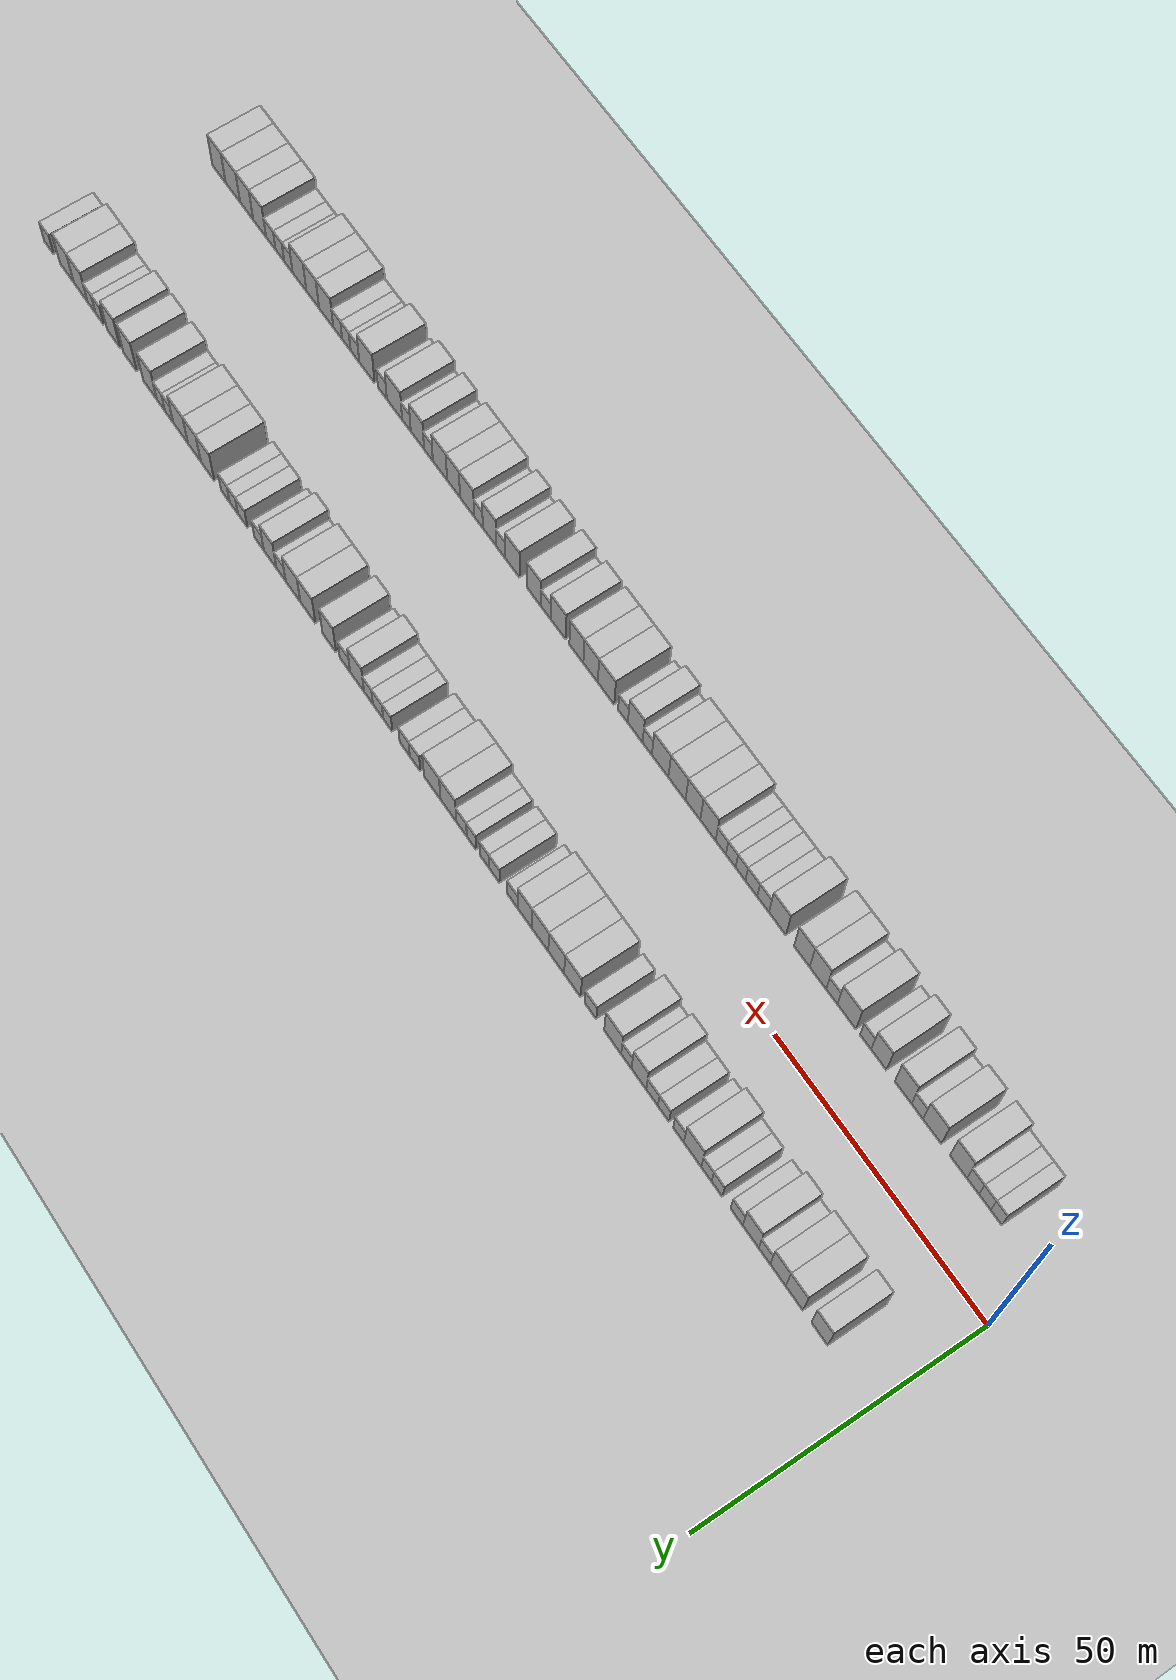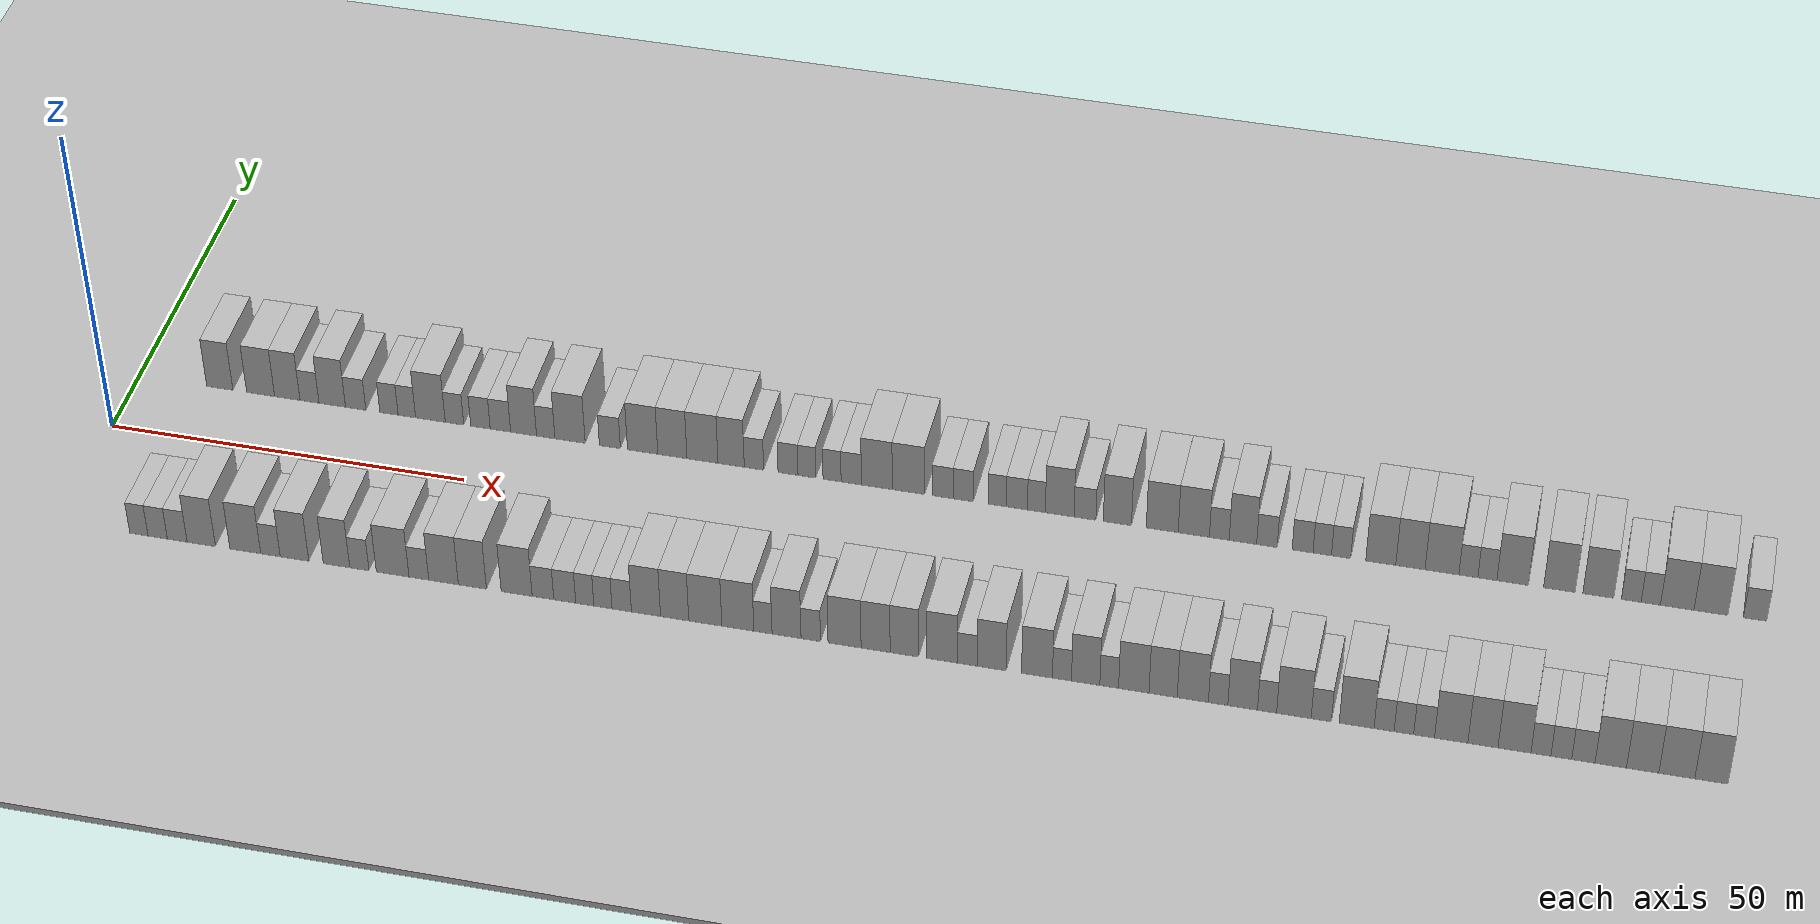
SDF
<?xml version="1.0" encoding="utf-8"?>

<sdf version="1.6">

   <world name="default">

      <gui fullscreen="0">

         <camera name="user_camera">

            <pose>-15 0 4.57585 0 0 0</pose>

            <view_controller>orbit</view_controller>

         </camera>

      </gui>

      <scene>

         <sky>

           <clouds>

             <speed>12</speed>

           </clouds>

         </sky>

         <ambient>0.4 0.4 0.4 1</ambient>

         <background>0.7 0.7 0.7 1</background>

         <shadows>1</shadows>

      </scene>

      <gravity>0 0 -9.8066</gravity>

      <magnetic_field>6e-06 2.3e-05 -4.2e-05</magnetic_field>

      <physics default="0" name="default_physics" type="ode">

         <ode>

            <solver>

               <type>quick</type>

               <iters>10</iters>

               <sor>1.0</sor>

               <use_dynamic_moi_rescaling>0</use_dynamic_moi_rescaling>

            </solver>

            <constraints>

               <cfm>0</cfm>

               <erp>0.2</erp>

               <contact_max_correcting_vel>100</contact_max_correcting_vel>

               <contact_surface_layer>0.001</contact_surface_layer>

            </constraints>

         </ode>

         <max_step_size>0.004</max_step_size>

         <real_time_factor>1</real_time_factor>

         <real_time_update_rate>250</real_time_update_rate>

      </physics>

      <light name="sun" type="directional">

         <cast_shadows>1</cast_shadows>

         <pose>0 0 10 0 0 0</pose>

         <diffuse>0.8 0.8 0.8 1</diffuse>

         <specular>0.2 0.2 0.2 1</specular>

         <attenuation>

            <range>1000</range>

            <constant>0.9</constant>

            <linear>0.01</linear>

            <quadratic>0.001</quadratic>

         </attenuation>

         <direction>-0.5 0.1 -0.9</direction>

      </light>

      <include>

         <name>ground_plane_1</name>

         <uri>model://HANNAS_ground_plane</uri>

         <pose>0 0 0  0 0 0</pose>

      </include>

      <include>

         <name>ground_plane_2</name>

         <uri>model://HANNAS_ground_plane</uri>

         <pose>100 0 0  0 0 0</pose>

      </include>

      <model name="building_1">

         <static>1</static>

         <pose frame="">11.8929 15.0000 0 0.000000 0.000000 1.570796</pose>

         <link name="link">

            <pose frame="">0 0 4.50 0 0 0</pose>

            <collision name="collision">

               <geometry>

                  <box>

                     <size>10.0000 3.7858 9.0000</size>

                  </box>

               </geometry>

               <max_contacts>10</max_contacts>

               <surface>

                  <contact>

                     <ode/>

                  </contact>

                  <bounce/>

                  <friction>

                     <torsional>

                        <ode/>

                     </torsional>

                     <ode/>

                  </friction>

               </surface>

            </collision>

            <visual name="visual">

               <cast_shadows>0</cast_shadows>

               <geometry>

                  <box>

                     <size>10.0000 3.7858 9.0000</size>

                  </box>

               </geometry>

               <material>

                  <script>

                     <uri>model://HANNAS_wall/materials/scripts</uri>

                     <uri>model://HANNAS_wall/materials/textures</uri>

                     <name>vrc/HANNAS_wall</name>

                  </script>

               </material>

            </visual>

            <self_collide>0</self_collide>

            <enable_wind>0</enable_wind>

            <kinematic>0</kinematic>

         </link>

      </model>

      <model name="building_2">

         <static>1</static>

         <pose frame="">17.8049 15.0000 0 0.000000 0.000000 1.570796</pose>

         <link name="link">

            <pose frame="">0 0 4.50 0 0 0</pose>

            <collision name="collision">

               <geometry>

                  <box>

                     <size>10.0000 4.0382 9.0000</size>

                  </box>

               </geometry>

               <max_contacts>10</max_contacts>

               <surface>

                  <contact>

                     <ode/>

                  </contact>

                  <bounce/>

                  <friction>

                     <torsional>

                        <ode/>

                     </torsional>

                     <ode/>

                  </friction>

               </surface>

            </collision>

            <visual name="visual">

               <cast_shadows>0</cast_shadows>

               <geometry>

                  <box>

                     <size>10.0000 4.0382 9.0000</size>

                  </box>

               </geometry>

               <material>

                  <script>

                     <uri>model://HANNAS_wall/materials/scripts</uri>

                     <uri>model://HANNAS_wall/materials/textures</uri>

                     <name>vrc/HANNAS_wall</name>

                  </script>

               </material>

            </visual>

            <self_collide>0</self_collide>

            <enable_wind>0</enable_wind>

            <kinematic>0</kinematic>

         </link>

      </model>

      <model name="building_3">

         <static>1</static>

         <pose frame="">21.6515 15.0000 0 0.000000 0.000000 1.570796</pose>

         <link name="link">

            <pose frame="">0 0 4.50 0 0 0</pose>

            <collision name="collision">

               <geometry>

                  <box>

                     <size>10.0000 3.6549 9.0000</size>

                  </box>

               </geometry>

               <max_contacts>10</max_contacts>

               <surface>

                  <contact>

                     <ode/>

                  </contact>

                  <bounce/>

                  <friction>

                     <torsional>

                        <ode/>

                     </torsional>

                     <ode/>

                  </friction>

               </surface>

            </collision>

            <visual name="visual">

               <cast_shadows>0</cast_shadows>

               <geometry>

                  <box>

                     <size>10.0000 3.6549 9.0000</size>

                  </box>

               </geometry>

               <material>

                  <script>

                     <uri>model://HANNAS_wall/materials/scripts</uri>

                     <uri>model://HANNAS_wall/materials/textures</uri>

                     <name>vrc/HANNAS_wall</name>

                  </script>

               </material>

            </visual>

            <self_collide>0</self_collide>

            <enable_wind>0</enable_wind>

            <kinematic>0</kinematic>

         </link>

      </model>

      <model name="building_4">

         <static>1</static>

         <pose frame="">24.8479 15.0000 0 0.000000 0.000000 1.570796</pose>

         <link name="link">

            <pose frame="">0 0 3.00 0 0 0</pose>

            <collision name="collision">

               <geometry>

                  <box>

                     <size>10.0000 2.7379 6.0000</size>

                  </box>

               </geometry>

               <max_contacts>10</max_contacts>

               <surface>

                  <contact>

                     <ode/>

                  </contact>

                  <bounce/>

                  <friction>

                     <torsional>

                        <ode/>

                     </torsional>

                     <ode/>

                  </friction>

               </surface>

            </collision>

            <visual name="visual">

               <cast_shadows>0</cast_shadows>

               <geometry>

                  <box>

                     <size>10.0000 2.7379 6.0000</size>

                  </box>

               </geometry>

               <material>

                  <script>

                     <uri>model://HANNAS_wall/materials/scripts</uri>

                     <uri>model://HANNAS_wall/materials/textures</uri>

                     <name>vrc/HANNAS_wall</name>

                  </script>

               </material>

            </visual>

            <self_collide>0</self_collide>

            <enable_wind>0</enable_wind>

            <kinematic>0</kinematic>

         </link>

      </model>

      <model name="building_5">

         <static>1</static>

         <pose frame="">28.1217 15.0000 0 0.000000 0.000000 1.570796</pose>

         <link name="link">

            <pose frame="">0 0 4.50 0 0 0</pose>

            <collision name="collision">

               <geometry>

                  <box>

                     <size>10.0000 3.8098 9.0000</size>

                  </box>

               </geometry>

               <max_contacts>10</max_contacts>

               <surface>

                  <contact>

                     <ode/>

                  </contact>

                  <bounce/>

                  <friction>

                     <torsional>

                        <ode/>

                     </torsional>

                     <ode/>

                  </friction>

               </surface>

            </collision>

            <visual name="visual">

               <cast_shadows>0</cast_shadows>

               <geometry>

                  <box>

                     <size>10.0000 3.8098 9.0000</size>

                  </box>

               </geometry>

               <material>

                  <script>

                     <uri>model://HANNAS_wall/materials/scripts</uri>

                     <uri>model://HANNAS_wall/materials/textures</uri>

                     <name>vrc/HANNAS_wall</name>

                  </script>

               </material>

            </visual>

            <self_collide>0</self_collide>

            <enable_wind>0</enable_wind>

            <kinematic>0</kinematic>

         </link>

      </model>

      <model name="building_6">

         <static>1</static>

         <pose frame="">31.4849 15.0000 0 0.000000 0.000000 1.570796</pose>

         <link name="link">

            <pose frame="">0 0 3.00 0 0 0</pose>

            <collision name="collision">

               <geometry>

                  <box>

                     <size>10.0000 2.9166 6.0000</size>

                  </box>

               </geometry>

               <max_contacts>10</max_contacts>

               <surface>

                  <contact>

                     <ode/>

                  </contact>

                  <bounce/>

                  <friction>

                     <torsional>

                        <ode/>

                     </torsional>

                     <ode/>

                  </friction>

               </surface>

            </collision>

            <visual name="visual">

               <cast_shadows>0</cast_shadows>

               <geometry>

                  <box>

                     <size>10.0000 2.9166 6.0000</size>

                  </box>

               </geometry>

               <material>

                  <script>

                     <uri>model://HANNAS_wall/materials/scripts</uri>

                     <uri>model://HANNAS_wall/materials/textures</uri>

                     <name>vrc/HANNAS_wall</name>

                  </script>

               </material>

            </visual>

            <self_collide>0</self_collide>

            <enable_wind>0</enable_wind>

            <kinematic>0</kinematic>

         </link>

      </model>

      <model name="building_7">

         <static>1</static>

         <pose frame="">36.2474 15.0000 0 0.000000 0.000000 1.570796</pose>

         <link name="link">

            <pose frame="">0 0 3.00 0 0 0</pose>

            <collision name="collision">

               <geometry>

                  <box>

                     <size>10.0000 2.6083 6.0000</size>

                  </box>

               </geometry>

               <max_contacts>10</max_contacts>

               <surface>

                  <contact>

                     <ode/>

                  </contact>

                  <bounce/>

                  <friction>

                     <torsional>

                        <ode/>

                     </torsional>

                     <ode/>

                  </friction>

               </surface>

            </collision>

            <visual name="visual">

               <cast_shadows>0</cast_shadows>

               <geometry>

                  <box>

                     <size>10.0000 2.6083 6.0000</size>

                  </box>

               </geometry>

               <material>

                  <script>

                     <uri>model://HANNAS_wall/materials/scripts</uri>

                     <uri>model://HANNAS_wall/materials/textures</uri>

                     <name>vrc/HANNAS_wall</name>

                  </script>

               </material>

            </visual>

            <self_collide>0</self_collide>

            <enable_wind>0</enable_wind>

            <kinematic>0</kinematic>

         </link>

      </model>

      <model name="building_8">

         <static>1</static>

         <pose frame="">38.7990 15.0000 0 0.000000 0.000000 1.570796</pose>

         <link name="link">

            <pose frame="">0 0 3.00 0 0 0</pose>

            <collision name="collision">

               <geometry>

                  <box>

                     <size>10.0000 2.4950 6.0000</size>

                  </box>

               </geometry>

               <max_contacts>10</max_contacts>

               <surface>

                  <contact>

                     <ode/>

                  </contact>

                  <bounce/>

                  <friction>

                     <torsional>

                        <ode/>

                     </torsional>

                     <ode/>

                  </friction>

               </surface>

            </collision>

            <visual name="visual">

               <cast_shadows>0</cast_shadows>

               <geometry>

                  <box>

                     <size>10.0000 2.4950 6.0000</size>

                  </box>

               </geometry>

               <material>

                  <script>

                     <uri>model://HANNAS_wall/materials/scripts</uri>

                     <uri>model://HANNAS_wall/materials/textures</uri>

                     <name>vrc/HANNAS_wall</name>

                  </script>

               </material>

            </visual>

            <self_collide>0</self_collide>

            <enable_wind>0</enable_wind>

            <kinematic>0</kinematic>

         </link>

      </model>

      <model name="building_9">

         <static>1</static>

         <pose frame="">42.1642 15.0000 0 0.000000 0.000000 1.570796</pose>

         <link name="link">

            <pose frame="">0 0 4.50 0 0 0</pose>

            <collision name="collision">

               <geometry>

                  <box>

                     <size>10.0000 4.2353 9.0000</size>

                  </box>

               </geometry>

               <max_contacts>10</max_contacts>

               <surface>

                  <contact>

                     <ode/>

                  </contact>

                  <bounce/>

                  <friction>

                     <torsional>

                        <ode/>

                     </torsional>

                     <ode/>

                  </friction>

               </surface>

            </collision>

            <visual name="visual">

               <cast_shadows>0</cast_shadows>

               <geometry>

                  <box>

                     <size>10.0000 4.2353 9.0000</size>

                  </box>

               </geometry>

               <material>

                  <script>

                     <uri>model://HANNAS_wall/materials/scripts</uri>

                     <uri>model://HANNAS_wall/materials/textures</uri>

                     <name>vrc/HANNAS_wall</name>

                  </script>

               </material>

            </visual>

            <self_collide>0</self_collide>

            <enable_wind>0</enable_wind>

            <kinematic>0</kinematic>

         </link>

      </model>

      <model name="building_10">

         <static>1</static>

         <pose frame="">45.5942 15.0000 0 0.000000 0.000000 1.570796</pose>

         <link name="link">

            <pose frame="">0 0 3.00 0 0 0</pose>

            <collision name="collision">

               <geometry>

                  <box>

                     <size>10.0000 2.6246 6.0000</size>

                  </box>

               </geometry>

               <max_contacts>10</max_contacts>

               <surface>

                  <contact>

                     <ode/>

                  </contact>

                  <bounce/>

                  <friction>

                     <torsional>

                        <ode/>

                     </torsional>

                     <ode/>

                  </friction>

               </surface>

            </collision>

            <visual name="visual">

               <cast_shadows>0</cast_shadows>

               <geometry>

                  <box>

                     <size>10.0000 2.6246 6.0000</size>

                  </box>

               </geometry>

               <material>

                  <script>

                     <uri>model://HANNAS_wall/materials/scripts</uri>

                     <uri>model://HANNAS_wall/materials/textures</uri>

                     <name>vrc/HANNAS_wall</name>

                  </script>

               </material>

            </visual>

            <self_collide>0</self_collide>

            <enable_wind>0</enable_wind>

            <kinematic>0</kinematic>

         </link>

      </model>

      <model name="building_11">

         <static>1</static>

         <pose frame="">49.2856 15.0000 0 0.000000 0.000000 1.570796</pose>

         <link name="link">

            <pose frame="">0 0 3.00 0 0 0</pose>

            <collision name="collision">

               <geometry>

                  <box>

                     <size>10.0000 2.7582 6.0000</size>

                  </box>

               </geometry>

               <max_contacts>10</max_contacts>

               <surface>

                  <contact>

                     <ode/>

                  </contact>

                  <bounce/>

                  <friction>

                     <torsional>

                        <ode/>

                     </torsional>

                     <ode/>

                  </friction>

               </surface>

            </collision>

            <visual name="visual">

               <cast_shadows>0</cast_shadows>

               <geometry>

                  <box>

                     <size>10.0000 2.7582 6.0000</size>

                  </box>

               </geometry>

               <material>

                  <script>

                     <uri>model://HANNAS_wall/materials/scripts</uri>

                     <uri>model://HANNAS_wall/materials/textures</uri>

                     <name>vrc/HANNAS_wall</name>

                  </script>

               </material>

            </visual>

            <self_collide>0</self_collide>

            <enable_wind>0</enable_wind>

            <kinematic>0</kinematic>

         </link>

      </model>

      <model name="building_12">

         <static>1</static>

         <pose frame="">52.1100 15.0000 0 0.000000 0.000000 1.570796</pose>

         <link name="link">

            <pose frame="">0 0 3.00 0 0 0</pose>

            <collision name="collision">

               <geometry>

                  <box>

                     <size>10.0000 2.8906 6.0000</size>

                  </box>

               </geometry>

               <max_contacts>10</max_contacts>

               <surface>

                  <contact>

                     <ode/>

                  </contact>

                  <bounce/>

                  <friction>

                     <torsional>

                        <ode/>

                     </torsional>

                     <ode/>

                  </friction>

               </surface>

            </collision>

            <visual name="visual">

               <cast_shadows>0</cast_shadows>

               <geometry>

                  <box>

                     <size>10.0000 2.8906 6.0000</size>

                  </box>

               </geometry>

               <material>

                  <script>

                     <uri>model://HANNAS_wall/materials/scripts</uri>

                     <uri>model://HANNAS_wall/materials/textures</uri>

                     <name>vrc/HANNAS_wall</name>

                  </script>

               </material>

            </visual>

            <self_collide>0</self_collide>

            <enable_wind>0</enable_wind>

            <kinematic>0</kinematic>

         </link>

      </model>

      <model name="building_13">

         <static>1</static>

         <pose frame="">55.3930 15.0000 0 0.000000 0.000000 1.570796</pose>

         <link name="link">

            <pose frame="">0 0 4.50 0 0 0</pose>

            <collision name="collision">

               <geometry>

                  <box>

                     <size>10.0000 3.6754 9.0000</size>

                  </box>

               </geometry>

               <max_contacts>10</max_contacts>

               <surface>

                  <contact>

                     <ode/>

                  </contact>

                  <bounce/>

                  <friction>

                     <torsional>

                        <ode/>

                     </torsional>

                     <ode/>

                  </friction>

               </surface>

            </collision>

            <visual name="visual">

               <cast_shadows>0</cast_shadows>

               <geometry>

                  <box>

                     <size>10.0000 3.6754 9.0000</size>

                  </box>

               </geometry>

               <material>

                  <script>

                     <uri>model://HANNAS_wall/materials/scripts</uri>

                     <uri>model://HANNAS_wall/materials/textures</uri>

                     <name>vrc/HANNAS_wall</name>

                  </script>

               </material>

            </visual>

            <self_collide>0</self_collide>

            <enable_wind>0</enable_wind>

            <kinematic>0</kinematic>

         </link>

      </model>

      <model name="building_14">

         <static>1</static>

         <pose frame="">58.5261 15.0000 0 0.000000 0.000000 1.570796</pose>

         <link name="link">

            <pose frame="">0 0 3.00 0 0 0</pose>

            <collision name="collision">

               <geometry>

                  <box>

                     <size>10.0000 2.5907 6.0000</size>

                  </box>

               </geometry>

               <max_contacts>10</max_contacts>

               <surface>

                  <contact>

                     <ode/>

                  </contact>

                  <bounce/>

                  <friction>

                     <torsional>

                        <ode/>

                     </torsional>

                     <ode/>

                  </friction>

               </surface>

            </collision>

            <visual name="visual">

               <cast_shadows>0</cast_shadows>

               <geometry>

                  <box>

                     <size>10.0000 2.5907 6.0000</size>

                  </box>

               </geometry>

               <material>

                  <script>

                     <uri>model://HANNAS_wall/materials/scripts</uri>

                     <uri>model://HANNAS_wall/materials/textures</uri>

                     <name>vrc/HANNAS_wall</name>

                  </script>

               </material>

            </visual>

            <self_collide>0</self_collide>

            <enable_wind>0</enable_wind>

            <kinematic>0</kinematic>

         </link>

      </model>

      <model name="building_15">

         <static>1</static>

         <pose frame="">61.9586 15.0000 0 0.000000 0.000000 1.570796</pose>

         <link name="link">

            <pose frame="">0 0 4.50 0 0 0</pose>

            <collision name="collision">

               <geometry>

                  <box>

                     <size>10.0000 4.2743 9.0000</size>

                  </box>

               </geometry>

               <max_contacts>10</max_contacts>

               <surface>

                  <contact>

                     <ode/>

                  </contact>

                  <bounce/>

                  <friction>

                     <torsional>

                        <ode/>

                     </torsional>

                     <ode/>

                  </friction>

               </surface>

            </collision>

            <visual name="visual">

               <cast_shadows>0</cast_shadows>

               <geometry>

                  <box>

                     <size>10.0000 4.2743 9.0000</size>

                  </box>

               </geometry>

               <material>

                  <script>

                     <uri>model://HANNAS_wall/materials/scripts</uri>

                     <uri>model://HANNAS_wall/materials/textures</uri>

                     <name>vrc/HANNAS_wall</name>

                  </script>

               </material>

            </visual>

            <self_collide>0</self_collide>

            <enable_wind>0</enable_wind>

            <kinematic>0</kinematic>

         </link>

      </model>

      <model name="building_16">

         <static>1</static>

         <pose frame="">67.5667 15.0000 0 0.000000 0.000000 1.570796</pose>

         <link name="link">

            <pose frame="">0 0 3.00 0 0 0</pose>

            <collision name="collision">

               <geometry>

                  <box>

                     <size>10.0000 2.9419 6.0000</size>

                  </box>

               </geometry>

               <max_contacts>10</max_contacts>

               <surface>

                  <contact>

                     <ode/>

                  </contact>

                  <bounce/>

                  <friction>

                     <torsional>

                        <ode/>

                     </torsional>

                     <ode/>

                  </friction>

               </surface>

            </collision>

            <visual name="visual">

               <cast_shadows>0</cast_shadows>

               <geometry>

                  <box>

                     <size>10.0000 2.9419 6.0000</size>

                  </box>

               </geometry>

               <material>

                  <script>

                     <uri>model://HANNAS_wall/materials/scripts</uri>

                     <uri>model://HANNAS_wall/materials/textures</uri>

                     <name>vrc/HANNAS_wall</name>

                  </script>

               </material>

            </visual>

            <self_collide>0</self_collide>

            <enable_wind>0</enable_wind>

            <kinematic>0</kinematic>

         </link>

      </model>

      <model name="building_17">

         <static>1</static>

         <pose frame="">72.1605 15.0000 0 0.000000 0.000000 1.570796</pose>

         <link name="link">

            <pose frame="">0 0 4.50 0 0 0</pose>

            <collision name="collision">

               <geometry>

                  <box>

                     <size>10.0000 4.2457 9.0000</size>

                  </box>

               </geometry>

               <max_contacts>10</max_contacts>

               <surface>

                  <contact>

                     <ode/>

                  </contact>

                  <bounce/>

                  <friction>

                     <torsional>

                        <ode/>

                     </torsional>

                     <ode/>

                  </friction>

               </surface>

            </collision>

            <visual name="visual">

               <cast_shadows>0</cast_shadows>

               <geometry>

                  <box>

                     <size>10.0000 4.2457 9.0000</size>

                  </box>

               </geometry>

               <material>

                  <script>

                     <uri>model://HANNAS_wall/materials/scripts</uri>

                     <uri>model://HANNAS_wall/materials/textures</uri>

                     <name>vrc/HANNAS_wall</name>

                  </script>

               </material>

            </visual>

            <self_collide>0</self_collide>

            <enable_wind>0</enable_wind>

            <kinematic>0</kinematic>

         </link>

      </model>

      <model name="building_18">

         <static>1</static>

         <pose frame="">76.3221 15.0000 0 0.000000 0.000000 1.570796</pose>

         <link name="link">

            <pose frame="">0 0 4.50 0 0 0</pose>

            <collision name="collision">

               <geometry>

                  <box>

                     <size>10.0000 4.0774 9.0000</size>

                  </box>

               </geometry>

               <max_contacts>10</max_contacts>

               <surface>

                  <contact>

                     <ode/>

                  </contact>

                  <bounce/>

                  <friction>

                     <torsional>

                        <ode/>

                     </torsional>

                     <ode/>

                  </friction>

               </surface>

            </collision>

            <visual name="visual">

               <cast_shadows>0</cast_shadows>

               <geometry>

                  <box>

                     <size>10.0000 4.0774 9.0000</size>

                  </box>

               </geometry>

               <material>

                  <script>

                     <uri>model://HANNAS_wall/materials/scripts</uri>

                     <uri>model://HANNAS_wall/materials/textures</uri>

                     <name>vrc/HANNAS_wall</name>

                  </script>

               </material>

            </visual>

            <self_collide>0</self_collide>

            <enable_wind>0</enable_wind>

            <kinematic>0</kinematic>

         </link>

      </model>

      <model name="building_19">

         <static>1</static>

         <pose frame="">80.5234 15.0000 0 0.000000 0.000000 1.570796</pose>

         <link name="link">

            <pose frame="">0 0 4.50 0 0 0</pose>

            <collision name="collision">

               <geometry>

                  <box>

                     <size>10.0000 4.3253 9.0000</size>

                  </box>

               </geometry>

               <max_contacts>10</max_contacts>

               <surface>

                  <contact>

                     <ode/>

                  </contact>

                  <bounce/>

                  <friction>

                     <torsional>

                        <ode/>

                     </torsional>

                     <ode/>

                  </friction>

               </surface>

            </collision>

            <visual name="visual">

               <cast_shadows>0</cast_shadows>

               <geometry>

                  <box>

                     <size>10.0000 4.3253 9.0000</size>

                  </box>

               </geometry>

               <material>

                  <script>

                     <uri>model://HANNAS_wall/materials/scripts</uri>

                     <uri>model://HANNAS_wall/materials/textures</uri>

                     <name>vrc/HANNAS_wall</name>

                  </script>

               </material>

            </visual>

            <self_collide>0</self_collide>

            <enable_wind>0</enable_wind>

            <kinematic>0</kinematic>

         </link>

      </model>

      <model name="building_20">

         <static>1</static>

         <pose frame="">84.5161 15.0000 0 0.000000 0.000000 1.570796</pose>

         <link name="link">

            <pose frame="">0 0 4.50 0 0 0</pose>

            <collision name="collision">

               <geometry>

                  <box>

                     <size>10.0000 3.6600 9.0000</size>

                  </box>

               </geometry>

               <max_contacts>10</max_contacts>

               <surface>

                  <contact>

                     <ode/>

                  </contact>

                  <bounce/>

                  <friction>

                     <torsional>

                        <ode/>

                     </torsional>

                     <ode/>

                  </friction>

               </surface>

            </collision>

            <visual name="visual">

               <cast_shadows>0</cast_shadows>

               <geometry>

                  <box>

                     <size>10.0000 3.6600 9.0000</size>

                  </box>

               </geometry>

               <material>

                  <script>

                     <uri>model://HANNAS_wall/materials/scripts</uri>

                     <uri>model://HANNAS_wall/materials/textures</uri>

                     <name>vrc/HANNAS_wall</name>

                  </script>

               </material>

            </visual>

            <self_collide>0</self_collide>

            <enable_wind>0</enable_wind>

            <kinematic>0</kinematic>

         </link>

      </model>

      <model name="building_21">

         <static>1</static>

         <pose frame="">87.6903 15.0000 0 0.000000 0.000000 1.570796</pose>

         <link name="link">

            <pose frame="">0 0 3.00 0 0 0</pose>

            <collision name="collision">

               <geometry>

                  <box>

                     <size>10.0000 2.6885 6.0000</size>

                  </box>

               </geometry>

               <max_contacts>10</max_contacts>

               <surface>

                  <contact>

                     <ode/>

                  </contact>

                  <bounce/>

                  <friction>

                     <torsional>

                        <ode/>

                     </torsional>

                     <ode/>

                  </friction>

               </surface>

            </collision>

            <visual name="visual">

               <cast_shadows>0</cast_shadows>

               <geometry>

                  <box>

                     <size>10.0000 2.6885 6.0000</size>

                  </box>

               </geometry>

               <material>

                  <script>

                     <uri>model://HANNAS_wall/materials/scripts</uri>

                     <uri>model://HANNAS_wall/materials/textures</uri>

                     <name>vrc/HANNAS_wall</name>

                  </script>

               </material>

            </visual>

            <self_collide>0</self_collide>

            <enable_wind>0</enable_wind>

            <kinematic>0</kinematic>

         </link>

      </model>

      <model name="building_22">

         <static>1</static>

         <pose frame="">92.4171 15.0000 0 0.000000 0.000000 1.570796</pose>

         <link name="link">

            <pose frame="">0 0 3.00 0 0 0</pose>

            <collision name="collision">

               <geometry>

                  <box>

                     <size>10.0000 2.7649 6.0000</size>

                  </box>

               </geometry>

               <max_contacts>10</max_contacts>

               <surface>

                  <contact>

                     <ode/>

                  </contact>

                  <bounce/>

                  <friction>

                     <torsional>

                        <ode/>

                     </torsional>

                     <ode/>

                  </friction>

               </surface>

            </collision>

            <visual name="visual">

               <cast_shadows>0</cast_shadows>

               <geometry>

                  <box>

                     <size>10.0000 2.7649 6.0000</size>

                  </box>

               </geometry>

               <material>

                  <script>

                     <uri>model://HANNAS_wall/materials/scripts</uri>

                     <uri>model://HANNAS_wall/materials/textures</uri>

                     <name>vrc/HANNAS_wall</name>

                  </script>

               </material>

            </visual>

            <self_collide>0</self_collide>

            <enable_wind>0</enable_wind>

            <kinematic>0</kinematic>

         </link>

      </model>

      <model name="building_23">

         <static>1</static>

         <pose frame="">95.0302 15.0000 0 0.000000 0.000000 1.570796</pose>

         <link name="link">

            <pose frame="">0 0 3.00 0 0 0</pose>

            <collision name="collision">

               <geometry>

                  <box>

                     <size>10.0000 2.4614 6.0000</size>

                  </box>

               </geometry>

               <max_contacts>10</max_contacts>

               <surface>

                  <contact>

                     <ode/>

                  </contact>

                  <bounce/>

                  <friction>

                     <torsional>

                        <ode/>

                     </torsional>

                     <ode/>

                  </friction>

               </surface>

            </collision>

            <visual name="visual">

               <cast_shadows>0</cast_shadows>

               <geometry>

                  <box>

                     <size>10.0000 2.4614 6.0000</size>

                  </box>

               </geometry>

               <material>

                  <script>

                     <uri>model://HANNAS_wall/materials/scripts</uri>

                     <uri>model://HANNAS_wall/materials/textures</uri>

                     <name>vrc/HANNAS_wall</name>

                  </script>

               </material>

            </visual>

            <self_collide>0</self_collide>

            <enable_wind>0</enable_wind>

            <kinematic>0</kinematic>

         </link>

      </model>

      <model name="building_24">

         <static>1</static>

         <pose frame="">98.5067 15.0000 0 0.000000 0.000000 1.570796</pose>

         <link name="link">

            <pose frame="">0 0 3.00 0 0 0</pose>

            <collision name="collision">

               <geometry>

                  <box>

                     <size>10.0000 2.4915 6.0000</size>

                  </box>

               </geometry>

               <max_contacts>10</max_contacts>

               <surface>

                  <contact>

                     <ode/>

                  </contact>

                  <bounce/>

                  <friction>

                     <torsional>

                        <ode/>

                     </torsional>

                     <ode/>

                  </friction>

               </surface>

            </collision>

            <visual name="visual">

               <cast_shadows>0</cast_shadows>

               <geometry>

                  <box>

                     <size>10.0000 2.4915 6.0000</size>

                  </box>

               </geometry>

               <material>

                  <script>

                     <uri>model://HANNAS_wall/materials/scripts</uri>

                     <uri>model://HANNAS_wall/materials/textures</uri>

                     <name>vrc/HANNAS_wall</name>

                  </script>

               </material>

            </visual>

            <self_collide>0</self_collide>

            <enable_wind>0</enable_wind>

            <kinematic>0</kinematic>

         </link>

      </model>

      <model name="building_25">

         <static>1</static>

         <pose frame="">101.1531 15.0000 0 0.000000 0.000000 1.570796</pose>

         <link name="link">

            <pose frame="">0 0 3.00 0 0 0</pose>

            <collision name="collision">

               <geometry>

                  <box>

                     <size>10.0000 2.8013 6.0000</size>

                  </box>

               </geometry>

               <max_contacts>10</max_contacts>

               <surface>

                  <contact>

                     <ode/>

                  </contact>

                  <bounce/>

                  <friction>

                     <torsional>

                        <ode/>

                     </torsional>

                     <ode/>

                  </friction>

               </surface>

            </collision>

            <visual name="visual">

               <cast_shadows>0</cast_shadows>

               <geometry>

                  <box>

                     <size>10.0000 2.8013 6.0000</size>

                  </box>

               </geometry>

               <material>

                  <script>

                     <uri>model://HANNAS_wall/materials/scripts</uri>

                     <uri>model://HANNAS_wall/materials/textures</uri>

                     <name>vrc/HANNAS_wall</name>

                  </script>

               </material>

            </visual>

            <self_collide>0</self_collide>

            <enable_wind>0</enable_wind>

            <kinematic>0</kinematic>

         </link>

      </model>

      <model name="building_26">

         <static>1</static>

         <pose frame="">104.6745 15.0000 0 0.000000 0.000000 1.570796</pose>

         <link name="link">

            <pose frame="">0 0 4.50 0 0 0</pose>

            <collision name="collision">

               <geometry>

                  <box>

                     <size>10.0000 4.2414 9.0000</size>

                  </box>

               </geometry>

               <max_contacts>10</max_contacts>

               <surface>

                  <contact>

                     <ode/>

                  </contact>

                  <bounce/>

                  <friction>

                     <torsional>

                        <ode/>

                     </torsional>

                     <ode/>

                  </friction>

               </surface>

            </collision>

            <visual name="visual">

               <cast_shadows>0</cast_shadows>

               <geometry>

                  <box>

                     <size>10.0000 4.2414 9.0000</size>

                  </box>

               </geometry>

               <material>

                  <script>

                     <uri>model://HANNAS_wall/materials/scripts</uri>

                     <uri>model://HANNAS_wall/materials/textures</uri>

                     <name>vrc/HANNAS_wall</name>

                  </script>

               </material>

            </visual>

            <self_collide>0</self_collide>

            <enable_wind>0</enable_wind>

            <kinematic>0</kinematic>

         </link>

      </model>

      <model name="building_27">

         <static>1</static>

         <pose frame="">109.0264 15.0000 0 0.000000 0.000000 1.570796</pose>

         <link name="link">

            <pose frame="">0 0 4.50 0 0 0</pose>

            <collision name="collision">

               <geometry>

                  <box>

                     <size>10.0000 4.4623 9.0000</size>

                  </box>

               </geometry>

               <max_contacts>10</max_contacts>

               <surface>

                  <contact>

                     <ode/>

                  </contact>

                  <bounce/>

                  <friction>

                     <torsional>

                        <ode/>

                     </torsional>

                     <ode/>

                  </friction>

               </surface>

            </collision>

            <visual name="visual">

               <cast_shadows>0</cast_shadows>

               <geometry>

                  <box>

                     <size>10.0000 4.4623 9.0000</size>

                  </box>

               </geometry>

               <material>

                  <script>

                     <uri>model://HANNAS_wall/materials/scripts</uri>

                     <uri>model://HANNAS_wall/materials/textures</uri>

                     <name>vrc/HANNAS_wall</name>

                  </script>

               </material>

            </visual>

            <self_collide>0</self_collide>

            <enable_wind>0</enable_wind>

            <kinematic>0</kinematic>

         </link>

      </model>

      <model name="building_28">

         <static>1</static>

         <pose frame="">113.6944 15.0000 0 0.000000 0.000000 1.570796</pose>

         <link name="link">

            <pose frame="">0 0 3.00 0 0 0</pose>

            <collision name="collision">

               <geometry>

                  <box>

                     <size>10.0000 2.8739 6.0000</size>

                  </box>

               </geometry>

               <max_contacts>10</max_contacts>

               <surface>

                  <contact>

                     <ode/>

                  </contact>

                  <bounce/>

                  <friction>

                     <torsional>

                        <ode/>

                     </torsional>

                     <ode/>

                  </friction>

               </surface>

            </collision>

            <visual name="visual">

               <cast_shadows>0</cast_shadows>

               <geometry>

                  <box>

                     <size>10.0000 2.8739 6.0000</size>

                  </box>

               </geometry>

               <material>

                  <script>

                     <uri>model://HANNAS_wall/materials/scripts</uri>

                     <uri>model://HANNAS_wall/materials/textures</uri>

                     <name>vrc/HANNAS_wall</name>

                  </script>

               </material>

            </visual>

            <self_collide>0</self_collide>

            <enable_wind>0</enable_wind>

            <kinematic>0</kinematic>

         </link>

      </model>

      <model name="building_29">

         <static>1</static>

         <pose frame="">116.5172 15.0000 0 0.000000 0.000000 1.570796</pose>

         <link name="link">

            <pose frame="">0 0 3.00 0 0 0</pose>

            <collision name="collision">

               <geometry>

                  <box>

                     <size>10.0000 2.7716 6.0000</size>

                  </box>

               </geometry>

               <max_contacts>10</max_contacts>

               <surface>

                  <contact>

                     <ode/>

                  </contact>

                  <bounce/>

                  <friction>

                     <torsional>

                        <ode/>

                     </torsional>

                     <ode/>

                  </friction>

               </surface>

            </collision>

            <visual name="visual">

               <cast_shadows>0</cast_shadows>

               <geometry>

                  <box>

                     <size>10.0000 2.7716 6.0000</size>

                  </box>

               </geometry>

               <material>

                  <script>

                     <uri>model://HANNAS_wall/materials/scripts</uri>

                     <uri>model://HANNAS_wall/materials/textures</uri>

                     <name>vrc/HANNAS_wall</name>

                  </script>

               </material>

            </visual>

            <self_collide>0</self_collide>

            <enable_wind>0</enable_wind>

            <kinematic>0</kinematic>

         </link>

      </model>

      <model name="building_30">

         <static>1</static>

         <pose frame="">121.1402 15.0000 0 0.000000 0.000000 1.570796</pose>

         <link name="link">

            <pose frame="">0 0 3.00 0 0 0</pose>

            <collision name="collision">

               <geometry>

                  <box>

                     <size>10.0000 2.4743 6.0000</size>

                  </box>

               </geometry>

               <max_contacts>10</max_contacts>

               <surface>

                  <contact>

                     <ode/>

                  </contact>

                  <bounce/>

                  <friction>

                     <torsional>

                        <ode/>

                     </torsional>

                     <ode/>

                  </friction>

               </surface>

            </collision>

            <visual name="visual">

               <cast_shadows>0</cast_shadows>

               <geometry>

                  <box>

                     <size>10.0000 2.4743 6.0000</size>

                  </box>

               </geometry>

               <material>

                  <script>

                     <uri>model://HANNAS_wall/materials/scripts</uri>

                     <uri>model://HANNAS_wall/materials/textures</uri>

                     <name>vrc/HANNAS_wall</name>

                  </script>

               </material>

            </visual>

            <self_collide>0</self_collide>

            <enable_wind>0</enable_wind>

            <kinematic>0</kinematic>

         </link>

      </model>

      <model name="building_31">

         <static>1</static>

         <pose frame="">123.8260 15.0000 0 0.000000 0.000000 1.570796</pose>

         <link name="link">

            <pose frame="">0 0 3.00 0 0 0</pose>

            <collision name="collision">

               <geometry>

                  <box>

                     <size>10.0000 2.8974 6.0000</size>

                  </box>

               </geometry>

               <max_contacts>10</max_contacts>

               <surface>

                  <contact>

                     <ode/>

                  </contact>

                  <bounce/>

                  <friction>

                     <torsional>

                        <ode/>

                     </torsional>

                     <ode/>

                  </friction>

               </surface>

            </collision>

            <visual name="visual">

               <cast_shadows>0</cast_shadows>

               <geometry>

                  <box>

                     <size>10.0000 2.8974 6.0000</size>

                  </box>

               </geometry>

               <material>

                  <script>

                     <uri>model://HANNAS_wall/materials/scripts</uri>

                     <uri>model://HANNAS_wall/materials/textures</uri>

                     <name>vrc/HANNAS_wall</name>

                  </script>

               </material>

            </visual>

            <self_collide>0</self_collide>

            <enable_wind>0</enable_wind>

            <kinematic>0</kinematic>

         </link>

      </model>

      <model name="building_32">

         <static>1</static>

         <pose frame="">126.4903 15.0000 0 0.000000 0.000000 1.570796</pose>

         <link name="link">

            <pose frame="">0 0 3.00 0 0 0</pose>

            <collision name="collision">

               <geometry>

                  <box>

                     <size>10.0000 2.4313 6.0000</size>

                  </box>

               </geometry>

               <max_contacts>10</max_contacts>

               <surface>

                  <contact>

                     <ode/>

                  </contact>

                  <bounce/>

                  <friction>

                     <torsional>

                        <ode/>

                     </torsional>

                     <ode/>

                  </friction>

               </surface>

            </collision>

            <visual name="visual">

               <cast_shadows>0</cast_shadows>

               <geometry>

                  <box>

                     <size>10.0000 2.4313 6.0000</size>

                  </box>

               </geometry>

               <material>

                  <script>

                     <uri>model://HANNAS_wall/materials/scripts</uri>

                     <uri>model://HANNAS_wall/materials/textures</uri>

                     <name>vrc/HANNAS_wall</name>

                  </script>

               </material>

            </visual>

            <self_collide>0</self_collide>

            <enable_wind>0</enable_wind>

            <kinematic>0</kinematic>

         </link>

      </model>

      <model name="building_33">

         <static>1</static>

         <pose frame="">129.6501 15.0000 0 0.000000 0.000000 1.570796</pose>

         <link name="link">

            <pose frame="">0 0 4.50 0 0 0</pose>

            <collision name="collision">

               <geometry>

                  <box>

                     <size>10.0000 3.8882 9.0000</size>

                  </box>

               </geometry>

               <max_contacts>10</max_contacts>

               <surface>

                  <contact>

                     <ode/>

                  </contact>

                  <bounce/>

                  <friction>

                     <torsional>

                        <ode/>

                     </torsional>

                     <ode/>

                  </friction>

               </surface>

            </collision>

            <visual name="visual">

               <cast_shadows>0</cast_shadows>

               <geometry>

                  <box>

                     <size>10.0000 3.8882 9.0000</size>

                  </box>

               </geometry>

               <material>

                  <script>

                     <uri>model://HANNAS_wall/materials/scripts</uri>

                     <uri>model://HANNAS_wall/materials/textures</uri>

                     <name>vrc/HANNAS_wall</name>

                  </script>

               </material>

            </visual>

            <self_collide>0</self_collide>

            <enable_wind>0</enable_wind>

            <kinematic>0</kinematic>

         </link>

      </model>

      <model name="building_34">

         <static>1</static>

         <pose frame="">133.0760 15.0000 0 0.000000 0.000000 1.570796</pose>

         <link name="link">

            <pose frame="">0 0 3.00 0 0 0</pose>

            <collision name="collision">

               <geometry>

                  <box>

                     <size>10.0000 2.9636 6.0000</size>

                  </box>

               </geometry>

               <max_contacts>10</max_contacts>

               <surface>

                  <contact>

                     <ode/>

                  </contact>

                  <bounce/>

                  <friction>

                     <torsional>

                        <ode/>

                     </torsional>

                     <ode/>

                  </friction>

               </surface>

            </collision>

            <visual name="visual">

               <cast_shadows>0</cast_shadows>

               <geometry>

                  <box>

                     <size>10.0000 2.9636 6.0000</size>

                  </box>

               </geometry>

               <material>

                  <script>

                     <uri>model://HANNAS_wall/materials/scripts</uri>

                     <uri>model://HANNAS_wall/materials/textures</uri>

                     <name>vrc/HANNAS_wall</name>

                  </script>

               </material>

            </visual>

            <self_collide>0</self_collide>

            <enable_wind>0</enable_wind>

            <kinematic>0</kinematic>

         </link>

      </model>

      <model name="building_35">

         <static>1</static>

         <pose frame="">137.4573 15.0000 0 0.000000 0.000000 1.570796</pose>

         <link name="link">

            <pose frame="">0 0 4.50 0 0 0</pose>

            <collision name="collision">

               <geometry>

                  <box>

                     <size>10.0000 3.7990 9.0000</size>

                  </box>

               </geometry>

               <max_contacts>10</max_contacts>

               <surface>

                  <contact>

                     <ode/>

                  </contact>

                  <bounce/>

                  <friction>

                     <torsional>

                        <ode/>

                     </torsional>

                     <ode/>

                  </friction>

               </surface>

            </collision>

            <visual name="visual">

               <cast_shadows>0</cast_shadows>

               <geometry>

                  <box>

                     <size>10.0000 3.7990 9.0000</size>

                  </box>

               </geometry>

               <material>

                  <script>

                     <uri>model://HANNAS_wall/materials/scripts</uri>

                     <uri>model://HANNAS_wall/materials/textures</uri>

                     <name>vrc/HANNAS_wall</name>

                  </script>

               </material>

            </visual>

            <self_collide>0</self_collide>

            <enable_wind>0</enable_wind>

            <kinematic>0</kinematic>

         </link>

      </model>

      <model name="building_36">

         <static>1</static>

         <pose frame="">143.5039 15.0000 0 0.000000 0.000000 1.570796</pose>

         <link name="link">

            <pose frame="">0 0 4.50 0 0 0</pose>

            <collision name="collision">

               <geometry>

                  <box>

                     <size>10.0000 4.2943 9.0000</size>

                  </box>

               </geometry>

               <max_contacts>10</max_contacts>

               <surface>

                  <contact>

                     <ode/>

                  </contact>

                  <bounce/>

                  <friction>

                     <torsional>

                        <ode/>

                     </torsional>

                     <ode/>

                  </friction>

               </surface>

            </collision>

            <visual name="visual">

               <cast_shadows>0</cast_shadows>

               <geometry>

                  <box>

                     <size>10.0000 4.2943 9.0000</size>

                  </box>

               </geometry>

               <material>

                  <script>

                     <uri>model://HANNAS_wall/materials/scripts</uri>

                     <uri>model://HANNAS_wall/materials/textures</uri>

                     <name>vrc/HANNAS_wall</name>

                  </script>

               </material>

            </visual>

            <self_collide>0</self_collide>

            <enable_wind>0</enable_wind>

            <kinematic>0</kinematic>

         </link>

      </model>

      <model name="building_37">

         <static>1</static>

         <pose frame="">147.7467 15.0000 0 0.000000 0.000000 1.570796</pose>

         <link name="link">

            <pose frame="">0 0 4.50 0 0 0</pose>

            <collision name="collision">

               <geometry>

                  <box>

                     <size>10.0000 4.1912 9.0000</size>

                  </box>

               </geometry>

               <max_contacts>10</max_contacts>

               <surface>

                  <contact>

                     <ode/>

                  </contact>

                  <bounce/>

                  <friction>

                     <torsional>

                        <ode/>

                     </torsional>

                     <ode/>

                  </friction>

               </surface>

            </collision>

            <visual name="visual">

               <cast_shadows>0</cast_shadows>

               <geometry>

                  <box>

                     <size>10.0000 4.1912 9.0000</size>

                  </box>

               </geometry>

               <material>

                  <script>

                     <uri>model://HANNAS_wall/materials/scripts</uri>

                     <uri>model://HANNAS_wall/materials/textures</uri>

                     <name>vrc/HANNAS_wall</name>

                  </script>

               </material>

            </visual>

            <self_collide>0</self_collide>

            <enable_wind>0</enable_wind>

            <kinematic>0</kinematic>

         </link>

      </model>

      <model name="building_38">

         <static>1</static>

         <pose frame="">151.1695 15.0000 0 0.000000 0.000000 1.570796</pose>

         <link name="link">

            <pose frame="">0 0 3.00 0 0 0</pose>

            <collision name="collision">

               <geometry>

                  <box>

                     <size>10.0000 2.6546 6.0000</size>

                  </box>

               </geometry>

               <max_contacts>10</max_contacts>

               <surface>

                  <contact>

                     <ode/>

                  </contact>

                  <bounce/>

                  <friction>

                     <torsional>

                        <ode/>

                     </torsional>

                     <ode/>

                  </friction>

               </surface>

            </collision>

            <visual name="visual">

               <cast_shadows>0</cast_shadows>

               <geometry>

                  <box>

                     <size>10.0000 2.6546 6.0000</size>

                  </box>

               </geometry>

               <material>

                  <script>

                     <uri>model://HANNAS_wall/materials/scripts</uri>

                     <uri>model://HANNAS_wall/materials/textures</uri>

                     <name>vrc/HANNAS_wall</name>

                  </script>

               </material>

            </visual>

            <self_collide>0</self_collide>

            <enable_wind>0</enable_wind>

            <kinematic>0</kinematic>

         </link>

      </model>

      <model name="building_39">

         <static>1</static>

         <pose frame="">154.3343 15.0000 0 0.000000 0.000000 1.570796</pose>

         <link name="link">

            <pose frame="">0 0 4.50 0 0 0</pose>

            <collision name="collision">

               <geometry>

                  <box>

                     <size>10.0000 3.6749 9.0000</size>

                  </box>

               </geometry>

               <max_contacts>10</max_contacts>

               <surface>

                  <contact>

                     <ode/>

                  </contact>

                  <bounce/>

                  <friction>

                     <torsional>

                        <ode/>

                     </torsional>

                     <ode/>

                  </friction>

               </surface>

            </collision>

            <visual name="visual">

               <cast_shadows>0</cast_shadows>

               <geometry>

                  <box>

                     <size>10.0000 3.6749 9.0000</size>

                  </box>

               </geometry>

               <material>

                  <script>

                     <uri>model://HANNAS_wall/materials/scripts</uri>

                     <uri>model://HANNAS_wall/materials/textures</uri>

                     <name>vrc/HANNAS_wall</name>

                  </script>

               </material>

            </visual>

            <self_collide>0</self_collide>

            <enable_wind>0</enable_wind>

            <kinematic>0</kinematic>

         </link>

      </model>

      <model name="building_40">

         <static>1</static>

         <pose frame="">157.5388 15.0000 0 0.000000 0.000000 1.570796</pose>

         <link name="link">

            <pose frame="">0 0 3.00 0 0 0</pose>

            <collision name="collision">

               <geometry>

                  <box>

                     <size>10.0000 2.7341 6.0000</size>

                  </box>

               </geometry>

               <max_contacts>10</max_contacts>

               <surface>

                  <contact>

                     <ode/>

                  </contact>

                  <bounce/>

                  <friction>

                     <torsional>

                        <ode/>

                     </torsional>

                     <ode/>

                  </friction>

               </surface>

            </collision>

            <visual name="visual">

               <cast_shadows>0</cast_shadows>

               <geometry>

                  <box>

                     <size>10.0000 2.7341 6.0000</size>

                  </box>

               </geometry>

               <material>

                  <script>

                     <uri>model://HANNAS_wall/materials/scripts</uri>

                     <uri>model://HANNAS_wall/materials/textures</uri>

                     <name>vrc/HANNAS_wall</name>

                  </script>

               </material>

            </visual>

            <self_collide>0</self_collide>

            <enable_wind>0</enable_wind>

            <kinematic>0</kinematic>

         </link>

      </model>

      <model name="building_41">

         <static>1</static>

         <pose frame="">162.2911 15.0000 0 0.000000 0.000000 1.570796</pose>

         <link name="link">

            <pose frame="">0 0 3.00 0 0 0</pose>

            <collision name="collision">

               <geometry>

                  <box>

                     <size>10.0000 2.7706 6.0000</size>

                  </box>

               </geometry>

               <max_contacts>10</max_contacts>

               <surface>

                  <contact>

                     <ode/>

                  </contact>

                  <bounce/>

                  <friction>

                     <torsional>

                        <ode/>

                     </torsional>

                     <ode/>

                  </friction>

               </surface>

            </collision>

            <visual name="visual">

               <cast_shadows>0</cast_shadows>

               <geometry>

                  <box>

                     <size>10.0000 2.7706 6.0000</size>

                  </box>

               </geometry>

               <material>

                  <script>

                     <uri>model://HANNAS_wall/materials/scripts</uri>

                     <uri>model://HANNAS_wall/materials/textures</uri>

                     <name>vrc/HANNAS_wall</name>

                  </script>

               </material>

            </visual>

            <self_collide>0</self_collide>

            <enable_wind>0</enable_wind>

            <kinematic>0</kinematic>

         </link>

      </model>

      <model name="building_42">

         <static>1</static>

         <pose frame="">164.9075 15.0000 0 0.000000 0.000000 1.570796</pose>

         <link name="link">

            <pose frame="">0 0 3.00 0 0 0</pose>

            <collision name="collision">

               <geometry>

                  <box>

                     <size>10.0000 2.4622 6.0000</size>

                  </box>

               </geometry>

               <max_contacts>10</max_contacts>

               <surface>

                  <contact>

                     <ode/>

                  </contact>

                  <bounce/>

                  <friction>

                     <torsional>

                        <ode/>

                     </torsional>

                     <ode/>

                  </friction>

               </surface>

            </collision>

            <visual name="visual">

               <cast_shadows>0</cast_shadows>

               <geometry>

                  <box>

                     <size>10.0000 2.4622 6.0000</size>

                  </box>

               </geometry>

               <material>

                  <script>

                     <uri>model://HANNAS_wall/materials/scripts</uri>

                     <uri>model://HANNAS_wall/materials/textures</uri>

                     <name>vrc/HANNAS_wall</name>

                  </script>

               </material>

            </visual>

            <self_collide>0</self_collide>

            <enable_wind>0</enable_wind>

            <kinematic>0</kinematic>

         </link>

      </model>

      <model name="building_43">

         <static>1</static>

         <pose frame="">167.4110 15.0000 0 0.000000 0.000000 1.570796</pose>

         <link name="link">

            <pose frame="">0 0 3.00 0 0 0</pose>

            <collision name="collision">

               <geometry>

                  <box>

                     <size>10.0000 2.5448 6.0000</size>

                  </box>

               </geometry>

               <max_contacts>10</max_contacts>

               <surface>

                  <contact>

                     <ode/>

                  </contact>

                  <bounce/>

                  <friction>

                     <torsional>

                        <ode/>

                     </torsional>

                     <ode/>

                  </friction>

               </surface>

            </collision>

            <visual name="visual">

               <cast_shadows>0</cast_shadows>

               <geometry>

                  <box>

                     <size>10.0000 2.5448 6.0000</size>

                  </box>

               </geometry>

               <material>

                  <script>

                     <uri>model://HANNAS_wall/materials/scripts</uri>

                     <uri>model://HANNAS_wall/materials/textures</uri>

                     <name>vrc/HANNAS_wall</name>

                  </script>

               </material>

            </visual>

            <self_collide>0</self_collide>

            <enable_wind>0</enable_wind>

            <kinematic>0</kinematic>

         </link>

      </model>

      <model name="building_44">

         <static>1</static>

         <pose frame="">172.6693 15.0000 0 0.000000 0.000000 1.570796</pose>

         <link name="link">

            <pose frame="">0 0 4.50 0 0 0</pose>

            <collision name="collision">

               <geometry>

                  <box>

                     <size>10.0000 3.9719 9.0000</size>

                  </box>

               </geometry>

               <max_contacts>10</max_contacts>

               <surface>

                  <contact>

                     <ode/>

                  </contact>

                  <bounce/>

                  <friction>

                     <torsional>

                        <ode/>

                     </torsional>

                     <ode/>

                  </friction>

               </surface>

            </collision>

            <visual name="visual">

               <cast_shadows>0</cast_shadows>

               <geometry>

                  <box>

                     <size>10.0000 3.9719 9.0000</size>

                  </box>

               </geometry>

               <material>

                  <script>

                     <uri>model://HANNAS_wall/materials/scripts</uri>

                     <uri>model://HANNAS_wall/materials/textures</uri>

                     <name>vrc/HANNAS_wall</name>

                  </script>

               </material>

            </visual>

            <self_collide>0</self_collide>

            <enable_wind>0</enable_wind>

            <kinematic>0</kinematic>

         </link>

      </model>

      <model name="building_45">

         <static>1</static>

         <pose frame="">176.5831 15.0000 0 0.000000 0.000000 1.570796</pose>

         <link name="link">

            <pose frame="">0 0 4.50 0 0 0</pose>

            <collision name="collision">

               <geometry>

                  <box>

                     <size>10.0000 3.8555 9.0000</size>

                  </box>

               </geometry>

               <max_contacts>10</max_contacts>

               <surface>

                  <contact>

                     <ode/>

                  </contact>

                  <bounce/>

                  <friction>

                     <torsional>

                        <ode/>

                     </torsional>

                     <ode/>

                  </friction>

               </surface>

            </collision>

            <visual name="visual">

               <cast_shadows>0</cast_shadows>

               <geometry>

                  <box>

                     <size>10.0000 3.8555 9.0000</size>

                  </box>

               </geometry>

               <material>

                  <script>

                     <uri>model://HANNAS_wall/materials/scripts</uri>

                     <uri>model://HANNAS_wall/materials/textures</uri>

                     <name>vrc/HANNAS_wall</name>

                  </script>

               </material>

            </visual>

            <self_collide>0</self_collide>

            <enable_wind>0</enable_wind>

            <kinematic>0</kinematic>

         </link>

      </model>

      <model name="building_46">

         <static>1</static>

         <pose frame="">180.7405 15.0000 0 0.000000 0.000000 1.570796</pose>

         <link name="link">

            <pose frame="">0 0 4.50 0 0 0</pose>

            <collision name="collision">

               <geometry>

                  <box>

                     <size>10.0000 4.4594 9.0000</size>

                  </box>

               </geometry>

               <max_contacts>10</max_contacts>

               <surface>

                  <contact>

                     <ode/>

                  </contact>

                  <bounce/>

                  <friction>

                     <torsional>

                        <ode/>

                     </torsional>

                     <ode/>

                  </friction>

               </surface>

            </collision>

            <visual name="visual">

               <cast_shadows>0</cast_shadows>

               <geometry>

                  <box>

                     <size>10.0000 4.4594 9.0000</size>

                  </box>

               </geometry>

               <material>

                  <script>

                     <uri>model://HANNAS_wall/materials/scripts</uri>

                     <uri>model://HANNAS_wall/materials/textures</uri>

                     <name>vrc/HANNAS_wall</name>

                  </script>

               </material>

            </visual>

            <self_collide>0</self_collide>

            <enable_wind>0</enable_wind>

            <kinematic>0</kinematic>

         </link>

      </model>

      <model name="building_47">

         <static>1</static>

         <pose frame="">184.2190 15.0000 0 0.000000 0.000000 1.570796</pose>

         <link name="link">

            <pose frame="">0 0 3.00 0 0 0</pose>

            <collision name="collision">

               <geometry>

                  <box>

                     <size>10.0000 2.4976 6.0000</size>

                  </box>

               </geometry>

               <max_contacts>10</max_contacts>

               <surface>

                  <contact>

                     <ode/>

                  </contact>

                  <bounce/>

                  <friction>

                     <torsional>

                        <ode/>

                     </torsional>

                     <ode/>

                  </friction>

               </surface>

            </collision>

            <visual name="visual">

               <cast_shadows>0</cast_shadows>

               <geometry>

                  <box>

                     <size>10.0000 2.4976 6.0000</size>

                  </box>

               </geometry>

               <material>

                  <script>

                     <uri>model://HANNAS_wall/materials/scripts</uri>

                     <uri>model://HANNAS_wall/materials/textures</uri>

                     <name>vrc/HANNAS_wall</name>

                  </script>

               </material>

            </visual>

            <self_collide>0</self_collide>

            <enable_wind>0</enable_wind>

            <kinematic>0</kinematic>

         </link>

      </model>

      <model name="building_48">

         <static>1</static>

         <pose frame="">186.7154 15.0000 0 0.000000 0.000000 1.570796</pose>

         <link name="link">

            <pose frame="">0 0 3.00 0 0 0</pose>

            <collision name="collision">

               <geometry>

                  <box>

                     <size>10.0000 2.4953 6.0000</size>

                  </box>

               </geometry>

               <max_contacts>10</max_contacts>

               <surface>

                  <contact>

                     <ode/>

                  </contact>

                  <bounce/>

                  <friction>

                     <torsional>

                        <ode/>

                     </torsional>

                     <ode/>

                  </friction>

               </surface>

            </collision>

            <visual name="visual">

               <cast_shadows>0</cast_shadows>

               <geometry>

                  <box>

                     <size>10.0000 2.4953 6.0000</size>

                  </box>

               </geometry>

               <material>

                  <script>

                     <uri>model://HANNAS_wall/materials/scripts</uri>

                     <uri>model://HANNAS_wall/materials/textures</uri>

                     <name>vrc/HANNAS_wall</name>

                  </script>

               </material>

            </visual>

            <self_collide>0</self_collide>

            <enable_wind>0</enable_wind>

            <kinematic>0</kinematic>

         </link>

      </model>

      <model name="building_49">

         <static>1</static>

         <pose frame="">190.0253 15.0000 0 0.000000 0.000000 1.570796</pose>

         <link name="link">

            <pose frame="">0 0 4.50 0 0 0</pose>

            <collision name="collision">

               <geometry>

                  <box>

                     <size>10.0000 4.1245 9.0000</size>

                  </box>

               </geometry>

               <max_contacts>10</max_contacts>

               <surface>

                  <contact>

                     <ode/>

                  </contact>

                  <bounce/>

                  <friction>

                     <torsional>

                        <ode/>

                     </torsional>

                     <ode/>

                  </friction>

               </surface>

            </collision>

            <visual name="visual">

               <cast_shadows>0</cast_shadows>

               <geometry>

                  <box>

                     <size>10.0000 4.1245 9.0000</size>

                  </box>

               </geometry>

               <material>

                  <script>

                     <uri>model://HANNAS_wall/materials/scripts</uri>

                     <uri>model://HANNAS_wall/materials/textures</uri>

                     <name>vrc/HANNAS_wall</name>

                  </script>

               </material>

            </visual>

            <self_collide>0</self_collide>

            <enable_wind>0</enable_wind>

            <kinematic>0</kinematic>

         </link>

      </model>

      <model name="building_50">

         <static>1</static>

         <pose frame="">196.1464 15.0000 0 0.000000 0.000000 1.570796</pose>

         <link name="link">

            <pose frame="">0 0 4.50 0 0 0</pose>

            <collision name="collision">

               <geometry>

                  <box>

                     <size>10.0000 4.1176 9.0000</size>

                  </box>

               </geometry>

               <max_contacts>10</max_contacts>

               <surface>

                  <contact>

                     <ode/>

                  </contact>

                  <bounce/>

                  <friction>

                     <torsional>

                        <ode/>

                     </torsional>

                     <ode/>

                  </friction>

               </surface>

            </collision>

            <visual name="visual">

               <cast_shadows>0</cast_shadows>

               <geometry>

                  <box>

                     <size>10.0000 4.1176 9.0000</size>

                  </box>

               </geometry>

               <material>

                  <script>

                     <uri>model://HANNAS_wall/materials/scripts</uri>

                     <uri>model://HANNAS_wall/materials/textures</uri>

                     <name>vrc/HANNAS_wall</name>

                  </script>

               </material>

            </visual>

            <self_collide>0</self_collide>

            <enable_wind>0</enable_wind>

            <kinematic>0</kinematic>

         </link>

      </model>

      <model name="building_51">

         <static>1</static>

         <pose frame="">201.2211 15.0000 0 0.000000 0.000000 1.570796</pose>

         <link name="link">

            <pose frame="">0 0 4.50 0 0 0</pose>

            <collision name="collision">

               <geometry>

                  <box>

                     <size>10.0000 4.0319 9.0000</size>

                  </box>

               </geometry>

               <max_contacts>10</max_contacts>

               <surface>

                  <contact>

                     <ode/>

                  </contact>

                  <bounce/>

                  <friction>

                     <torsional>

                        <ode/>

                     </torsional>

                     <ode/>

                  </friction>

               </surface>

            </collision>

            <visual name="visual">

               <cast_shadows>0</cast_shadows>

               <geometry>

                  <box>

                     <size>10.0000 4.0319 9.0000</size>

                  </box>

               </geometry>

               <material>

                  <script>

                     <uri>model://HANNAS_wall/materials/scripts</uri>

                     <uri>model://HANNAS_wall/materials/textures</uri>

                     <name>vrc/HANNAS_wall</name>

                  </script>

               </material>

            </visual>

            <self_collide>0</self_collide>

            <enable_wind>0</enable_wind>

            <kinematic>0</kinematic>

         </link>

      </model>

      <model name="building_52">

         <static>1</static>

         <pose frame="">205.5053 15.0000 0 0.000000 0.000000 1.570796</pose>

         <link name="link">

            <pose frame="">0 0 3.00 0 0 0</pose>

            <collision name="collision">

               <geometry>

                  <box>

                     <size>10.0000 2.5364 6.0000</size>

                  </box>

               </geometry>

               <max_contacts>10</max_contacts>

               <surface>

                  <contact>

                     <ode/>

                  </contact>

                  <bounce/>

                  <friction>

                     <torsional>

                        <ode/>

                     </torsional>

                     <ode/>

                  </friction>

               </surface>

            </collision>

            <visual name="visual">

               <cast_shadows>0</cast_shadows>

               <geometry>

                  <box>

                     <size>10.0000 2.5364 6.0000</size>

                  </box>

               </geometry>

               <material>

                  <script>

                     <uri>model://HANNAS_wall/materials/scripts</uri>

                     <uri>model://HANNAS_wall/materials/textures</uri>

                     <name>vrc/HANNAS_wall</name>

                  </script>

               </material>

            </visual>

            <self_collide>0</self_collide>

            <enable_wind>0</enable_wind>

            <kinematic>0</kinematic>

         </link>

      </model>

      <model name="building_53">

         <static>1</static>

         <pose frame="">208.0329 15.0000 0 0.000000 0.000000 1.570796</pose>

         <link name="link">

            <pose frame="">0 0 3.00 0 0 0</pose>

            <collision name="collision">

               <geometry>

                  <box>

                     <size>10.0000 2.5187 6.0000</size>

                  </box>

               </geometry>

               <max_contacts>10</max_contacts>

               <surface>

                  <contact>

                     <ode/>

                  </contact>

                  <bounce/>

                  <friction>

                     <torsional>

                        <ode/>

                     </torsional>

                     <ode/>

                  </friction>

               </surface>

            </collision>

            <visual name="visual">

               <cast_shadows>0</cast_shadows>

               <geometry>

                  <box>

                     <size>10.0000 2.5187 6.0000</size>

                  </box>

               </geometry>

               <material>

                  <script>

                     <uri>model://HANNAS_wall/materials/scripts</uri>

                     <uri>model://HANNAS_wall/materials/textures</uri>

                     <name>vrc/HANNAS_wall</name>

                  </script>

               </material>

            </visual>

            <self_collide>0</self_collide>

            <enable_wind>0</enable_wind>

            <kinematic>0</kinematic>

         </link>

      </model>

      <model name="building_54">

         <static>1</static>

         <pose frame="">211.4570 15.0000 0 0.000000 0.000000 1.570796</pose>

         <link name="link">

            <pose frame="">0 0 4.50 0 0 0</pose>

            <collision name="collision">

               <geometry>

                  <box>

                     <size>10.0000 4.3296 9.0000</size>

                  </box>

               </geometry>

               <max_contacts>10</max_contacts>

               <surface>

                  <contact>

                     <ode/>

                  </contact>

                  <bounce/>

                  <friction>

                     <torsional>

                        <ode/>

                     </torsional>

                     <ode/>

                  </friction>

               </surface>

            </collision>

            <visual name="visual">

               <cast_shadows>0</cast_shadows>

               <geometry>

                  <box>

                     <size>10.0000 4.3296 9.0000</size>

                  </box>

               </geometry>

               <material>

                  <script>

                     <uri>model://HANNAS_wall/materials/scripts</uri>

                     <uri>model://HANNAS_wall/materials/textures</uri>

                     <name>vrc/HANNAS_wall</name>

                  </script>

               </material>

            </visual>

            <self_collide>0</self_collide>

            <enable_wind>0</enable_wind>

            <kinematic>0</kinematic>

         </link>

      </model>

      <model name="building_55">

         <static>1</static>

         <pose frame="">215.8085 15.0000 0 0.000000 0.000000 1.570796</pose>

         <link name="link">

            <pose frame="">0 0 4.50 0 0 0</pose>

            <collision name="collision">

               <geometry>

                  <box>

                     <size>10.0000 4.3734 9.0000</size>

                  </box>

               </geometry>

               <max_contacts>10</max_contacts>

               <surface>

                  <contact>

                     <ode/>

                  </contact>

                  <bounce/>

                  <friction>

                     <torsional>

                        <ode/>

                     </torsional>

                     <ode/>

                  </friction>

               </surface>

            </collision>

            <visual name="visual">

               <cast_shadows>0</cast_shadows>

               <geometry>

                  <box>

                     <size>10.0000 4.3734 9.0000</size>

                  </box>

               </geometry>

               <material>

                  <script>

                     <uri>model://HANNAS_wall/materials/scripts</uri>

                     <uri>model://HANNAS_wall/materials/textures</uri>

                     <name>vrc/HANNAS_wall</name>

                  </script>

               </material>

            </visual>

            <self_collide>0</self_collide>

            <enable_wind>0</enable_wind>

            <kinematic>0</kinematic>

         </link>

      </model>

      <model name="building_56">

         <static>1</static>

         <pose frame="">221.4932 15.0000 0 0.000000 0.000000 1.570796</pose>

         <link name="link">

            <pose frame="">0 0 3.00 0 0 0</pose>

            <collision name="collision">

               <geometry>

                  <box>

                     <size>10.0000 2.9960 6.0000</size>

                  </box>

               </geometry>

               <max_contacts>10</max_contacts>

               <surface>

                  <contact>

                     <ode/>

                  </contact>

                  <bounce/>

                  <friction>

                     <torsional>

                        <ode/>

                     </torsional>

                     <ode/>

                  </friction>

               </surface>

            </collision>

            <visual name="visual">

               <cast_shadows>0</cast_shadows>

               <geometry>

                  <box>

                     <size>10.0000 2.9960 6.0000</size>

                  </box>

               </geometry>

               <material>

                  <script>

                     <uri>model://HANNAS_wall/materials/scripts</uri>

                     <uri>model://HANNAS_wall/materials/textures</uri>

                     <name>vrc/HANNAS_wall</name>

                  </script>

               </material>

            </visual>

            <self_collide>0</self_collide>

            <enable_wind>0</enable_wind>

            <kinematic>0</kinematic>

         </link>

      </model>

      <model name="building_57">

         <static>1</static>

         <pose frame="">11.2732 -15.0000 0 0.000000 0.000000 1.570796</pose>

         <link name="link">

            <pose frame="">0 0 3.00 0 0 0</pose>

            <collision name="collision">

               <geometry>

                  <box>

                     <size>10.0000 2.5463 6.0000</size>

                  </box>

               </geometry>

               <max_contacts>10</max_contacts>

               <surface>

                  <contact>

                     <ode/>

                  </contact>

                  <bounce/>

                  <friction>

                     <torsional>

                        <ode/>

                     </torsional>

                     <ode/>

                  </friction>

               </surface>

            </collision>

            <visual name="visual">

               <cast_shadows>0</cast_shadows>

               <geometry>

                  <box>

                     <size>10.0000 2.5463 6.0000</size>

                  </box>

               </geometry>

               <material>

                  <script>

                     <uri>model://HANNAS_wall/materials/scripts</uri>

                     <uri>model://HANNAS_wall/materials/textures</uri>

                     <name>vrc/HANNAS_wall</name>

                  </script>

               </material>

            </visual>

            <self_collide>0</self_collide>

            <enable_wind>0</enable_wind>

            <kinematic>0</kinematic>

         </link>

      </model>

      <model name="building_58">

         <static>1</static>

         <pose frame="">13.8984 -15.0000 0 0.000000 0.000000 1.570796</pose>

         <link name="link">

            <pose frame="">0 0 3.00 0 0 0</pose>

            <collision name="collision">

               <geometry>

                  <box>

                     <size>10.0000 2.7041 6.0000</size>

                  </box>

               </geometry>

               <max_contacts>10</max_contacts>

               <surface>

                  <contact>

                     <ode/>

                  </contact>

                  <bounce/>

                  <friction>

                     <torsional>

                        <ode/>

                     </torsional>

                     <ode/>

                  </friction>

               </surface>

            </collision>

            <visual name="visual">

               <cast_shadows>0</cast_shadows>

               <geometry>

                  <box>

                     <size>10.0000 2.7041 6.0000</size>

                  </box>

               </geometry>

               <material>

                  <script>

                     <uri>model://HANNAS_wall/materials/scripts</uri>

                     <uri>model://HANNAS_wall/materials/textures</uri>

                     <name>vrc/HANNAS_wall</name>

                  </script>

               </material>

            </visual>

            <self_collide>0</self_collide>

            <enable_wind>0</enable_wind>

            <kinematic>0</kinematic>

         </link>

      </model>

      <model name="building_59">

         <static>1</static>

         <pose frame="">16.6258 -15.0000 0 0.000000 0.000000 1.570796</pose>

         <link name="link">

            <pose frame="">0 0 3.00 0 0 0</pose>

            <collision name="collision">

               <geometry>

                  <box>

                     <size>10.0000 2.7507 6.0000</size>

                  </box>

               </geometry>

               <max_contacts>10</max_contacts>

               <surface>

                  <contact>

                     <ode/>

                  </contact>

                  <bounce/>

                  <friction>

                     <torsional>

                        <ode/>

                     </torsional>

                     <ode/>

                  </friction>

               </surface>

            </collision>

            <visual name="visual">

               <cast_shadows>0</cast_shadows>

               <geometry>

                  <box>

                     <size>10.0000 2.7507 6.0000</size>

                  </box>

               </geometry>

               <material>

                  <script>

                     <uri>model://HANNAS_wall/materials/scripts</uri>

                     <uri>model://HANNAS_wall/materials/textures</uri>

                     <name>vrc/HANNAS_wall</name>

                  </script>

               </material>

            </visual>

            <self_collide>0</self_collide>

            <enable_wind>0</enable_wind>

            <kinematic>0</kinematic>

         </link>

      </model>

      <model name="building_60">

         <static>1</static>

         <pose frame="">19.9818 -15.0000 0 0.000000 0.000000 1.570796</pose>

         <link name="link">

            <pose frame="">0 0 4.50 0 0 0</pose>

            <collision name="collision">

               <geometry>

                  <box>

                     <size>10.0000 3.9614 9.0000</size>

                  </box>

               </geometry>

               <max_contacts>10</max_contacts>

               <surface>

                  <contact>

                     <ode/>

                  </contact>

                  <bounce/>

                  <friction>

                     <torsional>

                        <ode/>

                     </torsional>

                     <ode/>

                  </friction>

               </surface>

            </collision>

            <visual name="visual">

               <cast_shadows>0</cast_shadows>

               <geometry>

                  <box>

                     <size>10.0000 3.9614 9.0000</size>

                  </box>

               </geometry>

               <material>

                  <script>

                     <uri>model://HANNAS_wall/materials/scripts</uri>

                     <uri>model://HANNAS_wall/materials/textures</uri>

                     <name>vrc/HANNAS_wall</name>

                  </script>

               </material>

            </visual>

            <self_collide>0</self_collide>

            <enable_wind>0</enable_wind>

            <kinematic>0</kinematic>

         </link>

      </model>

      <model name="building_61">

         <static>1</static>

         <pose frame="">26.1004 -15.0000 0 0.000000 0.000000 1.570796</pose>

         <link name="link">

            <pose frame="">0 0 4.50 0 0 0</pose>

            <collision name="collision">

               <geometry>

                  <box>

                     <size>10.0000 4.2758 9.0000</size>

                  </box>

               </geometry>

               <max_contacts>10</max_contacts>

               <surface>

                  <contact>

                     <ode/>

                  </contact>

                  <bounce/>

                  <friction>

                     <torsional>

                        <ode/>

                     </torsional>

                     <ode/>

                  </friction>

               </surface>

            </collision>

            <visual name="visual">

               <cast_shadows>0</cast_shadows>

               <geometry>

                  <box>

                     <size>10.0000 4.2758 9.0000</size>

                  </box>

               </geometry>

               <material>

                  <script>

                     <uri>model://HANNAS_wall/materials/scripts</uri>

                     <uri>model://HANNAS_wall/materials/textures</uri>

                     <name>vrc/HANNAS_wall</name>

                  </script>

               </material>

            </visual>

            <self_collide>0</self_collide>

            <enable_wind>0</enable_wind>

            <kinematic>0</kinematic>

         </link>

      </model>

      <model name="building_62">

         <static>1</static>

         <pose frame="">29.5896 -15.0000 0 0.000000 0.000000 1.570796</pose>

         <link name="link">

            <pose frame="">0 0 3.00 0 0 0</pose>

            <collision name="collision">

               <geometry>

                  <box>

                     <size>10.0000 2.7027 6.0000</size>

                  </box>

               </geometry>

               <max_contacts>10</max_contacts>

               <surface>

                  <contact>

                     <ode/>

                  </contact>

                  <bounce/>

                  <friction>

                     <torsional>

                        <ode/>

                     </torsional>

                     <ode/>

                  </friction>

               </surface>

            </collision>

            <visual name="visual">

               <cast_shadows>0</cast_shadows>

               <geometry>

                  <box>

                     <size>10.0000 2.7027 6.0000</size>

                  </box>

               </geometry>

               <material>

                  <script>

                     <uri>model://HANNAS_wall/materials/scripts</uri>

                     <uri>model://HANNAS_wall/materials/textures</uri>

                     <name>vrc/HANNAS_wall</name>

                  </script>

               </material>

            </visual>

            <self_collide>0</self_collide>

            <enable_wind>0</enable_wind>

            <kinematic>0</kinematic>

         </link>

      </model>

      <model name="building_63">

         <static>1</static>

         <pose frame="">32.9135 -15.0000 0 0.000000 0.000000 1.570796</pose>

         <link name="link">

            <pose frame="">0 0 4.50 0 0 0</pose>

            <collision name="collision">

               <geometry>

                  <box>

                     <size>10.0000 3.9450 9.0000</size>

                  </box>

               </geometry>

               <max_contacts>10</max_contacts>

               <surface>

                  <contact>

                     <ode/>

                  </contact>

                  <bounce/>

                  <friction>

                     <torsional>

                        <ode/>

                     </torsional>

                     <ode/>

                  </friction>

               </surface>

            </collision>

            <visual name="visual">

               <cast_shadows>0</cast_shadows>

               <geometry>

                  <box>

                     <size>10.0000 3.9450 9.0000</size>

                  </box>

               </geometry>

               <material>

                  <script>

                     <uri>model://HANNAS_wall/materials/scripts</uri>

                     <uri>model://HANNAS_wall/materials/textures</uri>

                     <name>vrc/HANNAS_wall</name>

                  </script>

               </material>

            </visual>

            <self_collide>0</self_collide>

            <enable_wind>0</enable_wind>

            <kinematic>0</kinematic>

         </link>

      </model>

      <model name="building_64">

         <static>1</static>

         <pose frame="">38.7111 -15.0000 0 0.000000 0.000000 1.570796</pose>

         <link name="link">

            <pose frame="">0 0 4.50 0 0 0</pose>

            <collision name="collision">

               <geometry>

                  <box>

                     <size>10.0000 3.6503 9.0000</size>

                  </box>

               </geometry>

               <max_contacts>10</max_contacts>

               <surface>

                  <contact>

                     <ode/>

                  </contact>

                  <bounce/>

                  <friction>

                     <torsional>

                        <ode/>

                     </torsional>

                     <ode/>

                  </friction>

               </surface>

            </collision>

            <visual name="visual">

               <cast_shadows>0</cast_shadows>

               <geometry>

                  <box>

                     <size>10.0000 3.6503 9.0000</size>

                  </box>

               </geometry>

               <material>

                  <script>

                     <uri>model://HANNAS_wall/materials/scripts</uri>

                     <uri>model://HANNAS_wall/materials/textures</uri>

                     <name>vrc/HANNAS_wall</name>

                  </script>

               </material>

            </visual>

            <self_collide>0</self_collide>

            <enable_wind>0</enable_wind>

            <kinematic>0</kinematic>

         </link>

      </model>

      <model name="building_65">

         <static>1</static>

         <pose frame="">41.8596 -15.0000 0 0.000000 0.000000 1.570796</pose>

         <link name="link">

            <pose frame="">0 0 3.00 0 0 0</pose>

            <collision name="collision">

               <geometry>

                  <box>

                     <size>10.0000 2.6468 6.0000</size>

                  </box>

               </geometry>

               <max_contacts>10</max_contacts>

               <surface>

                  <contact>

                     <ode/>

                  </contact>

                  <bounce/>

                  <friction>

                     <torsional>

                        <ode/>

                     </torsional>

                     <ode/>

                  </friction>

               </surface>

            </collision>

            <visual name="visual">

               <cast_shadows>0</cast_shadows>

               <geometry>

                  <box>

                     <size>10.0000 2.6468 6.0000</size>

                  </box>

               </geometry>

               <material>

                  <script>

                     <uri>model://HANNAS_wall/materials/scripts</uri>

                     <uri>model://HANNAS_wall/materials/textures</uri>

                     <name>vrc/HANNAS_wall</name>

                  </script>

               </material>

            </visual>

            <self_collide>0</self_collide>

            <enable_wind>0</enable_wind>

            <kinematic>0</kinematic>

         </link>

      </model>

      <model name="building_66">

         <static>1</static>

         <pose frame="">46.4245 -15.0000 0 0.000000 0.000000 1.570796</pose>

         <link name="link">

            <pose frame="">0 0 4.50 0 0 0</pose>

            <collision name="collision">

               <geometry>

                  <box>

                     <size>10.0000 4.4829 9.0000</size>

                  </box>

               </geometry>

               <max_contacts>10</max_contacts>

               <surface>

                  <contact>

                     <ode/>

                  </contact>

                  <bounce/>

                  <friction>

                     <torsional>

                        <ode/>

                     </torsional>

                     <ode/>

                  </friction>

               </surface>

            </collision>

            <visual name="visual">

               <cast_shadows>0</cast_shadows>

               <geometry>

                  <box>

                     <size>10.0000 4.4829 9.0000</size>

                  </box>

               </geometry>

               <material>

                  <script>

                     <uri>model://HANNAS_wall/materials/scripts</uri>

                     <uri>model://HANNAS_wall/materials/textures</uri>

                     <name>vrc/HANNAS_wall</name>

                  </script>

               </material>

            </visual>

            <self_collide>0</self_collide>

            <enable_wind>0</enable_wind>

            <kinematic>0</kinematic>

         </link>

      </model>

      <model name="building_67">

         <static>1</static>

         <pose frame="">50.0160 -15.0000 0 0.000000 0.000000 1.570796</pose>

         <link name="link">

            <pose frame="">0 0 3.00 0 0 0</pose>

            <collision name="collision">

               <geometry>

                  <box>

                     <size>10.0000 2.7002 6.0000</size>

                  </box>

               </geometry>

               <max_contacts>10</max_contacts>

               <surface>

                  <contact>

                     <ode/>

                  </contact>

                  <bounce/>

                  <friction>

                     <torsional>

                        <ode/>

                     </torsional>

                     <ode/>

                  </friction>

               </surface>

            </collision>

            <visual name="visual">

               <cast_shadows>0</cast_shadows>

               <geometry>

                  <box>

                     <size>10.0000 2.7002 6.0000</size>

                  </box>

               </geometry>

               <material>

                  <script>

                     <uri>model://HANNAS_wall/materials/scripts</uri>

                     <uri>model://HANNAS_wall/materials/textures</uri>

                     <name>vrc/HANNAS_wall</name>

                  </script>

               </material>

            </visual>

            <self_collide>0</self_collide>

            <enable_wind>0</enable_wind>

            <kinematic>0</kinematic>

         </link>

      </model>

      <model name="building_68">

         <static>1</static>

         <pose frame="">53.3879 -15.0000 0 0.000000 0.000000 1.570796</pose>

         <link name="link">

            <pose frame="">0 0 4.50 0 0 0</pose>

            <collision name="collision">

               <geometry>

                  <box>

                     <size>10.0000 4.0436 9.0000</size>

                  </box>

               </geometry>

               <max_contacts>10</max_contacts>

               <surface>

                  <contact>

                     <ode/>

                  </contact>

                  <bounce/>

                  <friction>

                     <torsional>

                        <ode/>

                     </torsional>

                     <ode/>

                  </friction>

               </surface>

            </collision>

            <visual name="visual">

               <cast_shadows>0</cast_shadows>

               <geometry>

                  <box>

                     <size>10.0000 4.0436 9.0000</size>

                  </box>

               </geometry>

               <material>

                  <script>

                     <uri>model://HANNAS_wall/materials/scripts</uri>

                     <uri>model://HANNAS_wall/materials/textures</uri>

                     <name>vrc/HANNAS_wall</name>

                  </script>

               </material>

            </visual>

            <self_collide>0</self_collide>

            <enable_wind>0</enable_wind>

            <kinematic>0</kinematic>

         </link>

      </model>

      <model name="building_69">

         <static>1</static>

         <pose frame="">57.3271 -15.0000 0 0.000000 0.000000 1.570796</pose>

         <link name="link">

            <pose frame="">0 0 4.50 0 0 0</pose>

            <collision name="collision">

               <geometry>

                  <box>

                     <size>10.0000 3.8349 9.0000</size>

                  </box>

               </geometry>

               <max_contacts>10</max_contacts>

               <surface>

                  <contact>

                     <ode/>

                  </contact>

                  <bounce/>

                  <friction>

                     <torsional>

                        <ode/>

                     </torsional>

                     <ode/>

                  </friction>

               </surface>

            </collision>

            <visual name="visual">

               <cast_shadows>0</cast_shadows>

               <geometry>

                  <box>

                     <size>10.0000 3.8349 9.0000</size>

                  </box>

               </geometry>

               <material>

                  <script>

                     <uri>model://HANNAS_wall/materials/scripts</uri>

                     <uri>model://HANNAS_wall/materials/textures</uri>

                     <name>vrc/HANNAS_wall</name>

                  </script>

               </material>

            </visual>

            <self_collide>0</self_collide>

            <enable_wind>0</enable_wind>

            <kinematic>0</kinematic>

         </link>

      </model>

      <model name="building_70">

         <static>1</static>

         <pose frame="">63.3466 -15.0000 0 0.000000 0.000000 1.570796</pose>

         <link name="link">

            <pose frame="">0 0 4.50 0 0 0</pose>

            <collision name="collision">

               <geometry>

                  <box>

                     <size>10.0000 4.2040 9.0000</size>

                  </box>

               </geometry>

               <max_contacts>10</max_contacts>

               <surface>

                  <contact>

                     <ode/>

                  </contact>

                  <bounce/>

                  <friction>

                     <torsional>

                        <ode/>

                     </torsional>

                     <ode/>

                  </friction>

               </surface>

            </collision>

            <visual name="visual">

               <cast_shadows>0</cast_shadows>

               <geometry>

                  <box>

                     <size>10.0000 4.2040 9.0000</size>

                  </box>

               </geometry>

               <material>

                  <script>

                     <uri>model://HANNAS_wall/materials/scripts</uri>

                     <uri>model://HANNAS_wall/materials/textures</uri>

                     <name>vrc/HANNAS_wall</name>

                  </script>

               </material>

            </visual>

            <self_collide>0</self_collide>

            <enable_wind>0</enable_wind>

            <kinematic>0</kinematic>

         </link>

      </model>

      <model name="building_71">

         <static>1</static>

         <pose frame="">66.9137 -15.0000 0 0.000000 0.000000 1.570796</pose>

         <link name="link">

            <pose frame="">0 0 3.00 0 0 0</pose>

            <collision name="collision">

               <geometry>

                  <box>

                     <size>10.0000 2.9303 6.0000</size>

                  </box>

               </geometry>

               <max_contacts>10</max_contacts>

               <surface>

                  <contact>

                     <ode/>

                  </contact>

                  <bounce/>

                  <friction>

                     <torsional>

                        <ode/>

                     </torsional>

                     <ode/>

                  </friction>

               </surface>

            </collision>

            <visual name="visual">

               <cast_shadows>0</cast_shadows>

               <geometry>

                  <box>

                     <size>10.0000 2.9303 6.0000</size>

                  </box>

               </geometry>

               <material>

                  <script>

                     <uri>model://HANNAS_wall/materials/scripts</uri>

                     <uri>model://HANNAS_wall/materials/textures</uri>

                     <name>vrc/HANNAS_wall</name>

                  </script>

               </material>

            </visual>

            <self_collide>0</self_collide>

            <enable_wind>0</enable_wind>

            <kinematic>0</kinematic>

         </link>

      </model>

      <model name="building_72">

         <static>1</static>

         <pose frame="">69.8640 -15.0000 0 0.000000 0.000000 1.570796</pose>

         <link name="link">

            <pose frame="">0 0 3.00 0 0 0</pose>

            <collision name="collision">

               <geometry>

                  <box>

                     <size>10.0000 2.9703 6.0000</size>

                  </box>

               </geometry>

               <max_contacts>10</max_contacts>

               <surface>

                  <contact>

                     <ode/>

                  </contact>

                  <bounce/>

                  <friction>

                     <torsional>

                        <ode/>

                     </torsional>

                     <ode/>

                  </friction>

               </surface>

            </collision>

            <visual name="visual">

               <cast_shadows>0</cast_shadows>

               <geometry>

                  <box>

                     <size>10.0000 2.9703 6.0000</size>

                  </box>

               </geometry>

               <material>

                  <script>

                     <uri>model://HANNAS_wall/materials/scripts</uri>

                     <uri>model://HANNAS_wall/materials/textures</uri>

                     <name>vrc/HANNAS_wall</name>

                  </script>

               </material>

            </visual>

            <self_collide>0</self_collide>

            <enable_wind>0</enable_wind>

            <kinematic>0</kinematic>

         </link>

      </model>

      <model name="building_73">

         <static>1</static>

         <pose frame="">72.5746 -15.0000 0 0.000000 0.000000 1.570796</pose>

         <link name="link">

            <pose frame="">0 0 3.00 0 0 0</pose>

            <collision name="collision">

               <geometry>

                  <box>

                     <size>10.0000 2.4508 6.0000</size>

                  </box>

               </geometry>

               <max_contacts>10</max_contacts>

               <surface>

                  <contact>

                     <ode/>

                  </contact>

                  <bounce/>

                  <friction>

                     <torsional>

                        <ode/>

                     </torsional>

                     <ode/>

                  </friction>

               </surface>

            </collision>

            <visual name="visual">

               <cast_shadows>0</cast_shadows>

               <geometry>

                  <box>

                     <size>10.0000 2.4508 6.0000</size>

                  </box>

               </geometry>

               <material>

                  <script>

                     <uri>model://HANNAS_wall/materials/scripts</uri>

                     <uri>model://HANNAS_wall/materials/textures</uri>

                     <name>vrc/HANNAS_wall</name>

                  </script>

               </material>

            </visual>

            <self_collide>0</self_collide>

            <enable_wind>0</enable_wind>

            <kinematic>0</kinematic>

         </link>

      </model>

      <model name="building_74">

         <static>1</static>

         <pose frame="">75.0219 -15.0000 0 0.000000 0.000000 1.570796</pose>

         <link name="link">

            <pose frame="">0 0 3.00 0 0 0</pose>

            <collision name="collision">

               <geometry>

                  <box>

                     <size>10.0000 2.4439 6.0000</size>

                  </box>

               </geometry>

               <max_contacts>10</max_contacts>

               <surface>

                  <contact>

                     <ode/>

                  </contact>

                  <bounce/>

                  <friction>

                     <torsional>

                        <ode/>

                     </torsional>

                     <ode/>

                  </friction>

               </surface>

            </collision>

            <visual name="visual">

               <cast_shadows>0</cast_shadows>

               <geometry>

                  <box>

                     <size>10.0000 2.4439 6.0000</size>

                  </box>

               </geometry>

               <material>

                  <script>

                     <uri>model://HANNAS_wall/materials/scripts</uri>

                     <uri>model://HANNAS_wall/materials/textures</uri>

                     <name>vrc/HANNAS_wall</name>

                  </script>

               </material>

            </visual>

            <self_collide>0</self_collide>

            <enable_wind>0</enable_wind>

            <kinematic>0</kinematic>

         </link>

      </model>

      <model name="building_75">

         <static>1</static>

         <pose frame="">77.5524 -15.0000 0 0.000000 0.000000 1.570796</pose>

         <link name="link">

            <pose frame="">0 0 3.00 0 0 0</pose>

            <collision name="collision">

               <geometry>

                  <box>

                     <size>10.0000 2.6172 6.0000</size>

                  </box>

               </geometry>

               <max_contacts>10</max_contacts>

               <surface>

                  <contact>

                     <ode/>

                  </contact>

                  <bounce/>

                  <friction>

                     <torsional>

                        <ode/>

                     </torsional>

                     <ode/>

                  </friction>

               </surface>

            </collision>

            <visual name="visual">

               <cast_shadows>0</cast_shadows>

               <geometry>

                  <box>

                     <size>10.0000 2.6172 6.0000</size>

                  </box>

               </geometry>

               <material>

                  <script>

                     <uri>model://HANNAS_wall/materials/scripts</uri>

                     <uri>model://HANNAS_wall/materials/textures</uri>

                     <name>vrc/HANNAS_wall</name>

                  </script>

               </material>

            </visual>

            <self_collide>0</self_collide>

            <enable_wind>0</enable_wind>

            <kinematic>0</kinematic>

         </link>

      </model>

      <model name="building_76">

         <static>1</static>

         <pose frame="">80.8176 -15.0000 0 0.000000 0.000000 1.570796</pose>

         <link name="link">

            <pose frame="">0 0 4.50 0 0 0</pose>

            <collision name="collision">

               <geometry>

                  <box>

                     <size>10.0000 3.9131 9.0000</size>

                  </box>

               </geometry>

               <max_contacts>10</max_contacts>

               <surface>

                  <contact>

                     <ode/>

                  </contact>

                  <bounce/>

                  <friction>

                     <torsional>

                        <ode/>

                     </torsional>

                     <ode/>

                  </friction>

               </surface>

            </collision>

            <visual name="visual">

               <cast_shadows>0</cast_shadows>

               <geometry>

                  <box>

                     <size>10.0000 3.9131 9.0000</size>

                  </box>

               </geometry>

               <material>

                  <script>

                     <uri>model://HANNAS_wall/materials/scripts</uri>

                     <uri>model://HANNAS_wall/materials/textures</uri>

                     <name>vrc/HANNAS_wall</name>

                  </script>

               </material>

            </visual>

            <self_collide>0</self_collide>

            <enable_wind>0</enable_wind>

            <kinematic>0</kinematic>

         </link>

      </model>

      <model name="building_77">

         <static>1</static>

         <pose frame="">84.6668 -15.0000 0 0.000000 0.000000 1.570796</pose>

         <link name="link">

            <pose frame="">0 0 4.50 0 0 0</pose>

            <collision name="collision">

               <geometry>

                  <box>

                     <size>10.0000 3.7854 9.0000</size>

                  </box>

               </geometry>

               <max_contacts>10</max_contacts>

               <surface>

                  <contact>

                     <ode/>

                  </contact>

                  <bounce/>

                  <friction>

                     <torsional>

                        <ode/>

                     </torsional>

                     <ode/>

                  </friction>

               </surface>

            </collision>

            <visual name="visual">

               <cast_shadows>0</cast_shadows>

               <geometry>

                  <box>

                     <size>10.0000 3.7854 9.0000</size>

                  </box>

               </geometry>

               <material>

                  <script>

                     <uri>model://HANNAS_wall/materials/scripts</uri>

                     <uri>model://HANNAS_wall/materials/textures</uri>

                     <name>vrc/HANNAS_wall</name>

                  </script>

               </material>

            </visual>

            <self_collide>0</self_collide>

            <enable_wind>0</enable_wind>

            <kinematic>0</kinematic>

         </link>

      </model>

      <model name="building_78">

         <static>1</static>

         <pose frame="">88.7731 -15.0000 0 0.000000 0.000000 1.570796</pose>

         <link name="link">

            <pose frame="">0 0 4.50 0 0 0</pose>

            <collision name="collision">

               <geometry>

                  <box>

                     <size>10.0000 4.4270 9.0000</size>

                  </box>

               </geometry>

               <max_contacts>10</max_contacts>

               <surface>

                  <contact>

                     <ode/>

                  </contact>

                  <bounce/>

                  <friction>

                     <torsional>

                        <ode/>

                     </torsional>

                     <ode/>

                  </friction>

               </surface>

            </collision>

            <visual name="visual">

               <cast_shadows>0</cast_shadows>

               <geometry>

                  <box>

                     <size>10.0000 4.4270 9.0000</size>

                  </box>

               </geometry>

               <material>

                  <script>

                     <uri>model://HANNAS_wall/materials/scripts</uri>

                     <uri>model://HANNAS_wall/materials/textures</uri>

                     <name>vrc/HANNAS_wall</name>

                  </script>

               </material>

            </visual>

            <self_collide>0</self_collide>

            <enable_wind>0</enable_wind>

            <kinematic>0</kinematic>

         </link>

      </model>

      <model name="building_79">

         <static>1</static>

         <pose frame="">93.1212 -15.0000 0 0.000000 0.000000 1.570796</pose>

         <link name="link">

            <pose frame="">0 0 4.50 0 0 0</pose>

            <collision name="collision">

               <geometry>

                  <box>

                     <size>10.0000 4.2693 9.0000</size>

                  </box>

               </geometry>

               <max_contacts>10</max_contacts>

               <surface>

                  <contact>

                     <ode/>

                  </contact>

                  <bounce/>

                  <friction>

                     <torsional>

                        <ode/>

                     </torsional>

                     <ode/>

                  </friction>

               </surface>

            </collision>

            <visual name="visual">

               <cast_shadows>0</cast_shadows>

               <geometry>

                  <box>

                     <size>10.0000 4.2693 9.0000</size>

                  </box>

               </geometry>

               <material>

                  <script>

                     <uri>model://HANNAS_wall/materials/scripts</uri>

                     <uri>model://HANNAS_wall/materials/textures</uri>

                     <name>vrc/HANNAS_wall</name>

                  </script>

               </material>

            </visual>

            <self_collide>0</self_collide>

            <enable_wind>0</enable_wind>

            <kinematic>0</kinematic>

         </link>

      </model>

      <model name="building_80">

         <static>1</static>

         <pose frame="">96.4669 -15.0000 0 0.000000 0.000000 1.570796</pose>

         <link name="link">

            <pose frame="">0 0 3.00 0 0 0</pose>

            <collision name="collision">

               <geometry>

                  <box>

                     <size>10.0000 2.4221 6.0000</size>

                  </box>

               </geometry>

               <max_contacts>10</max_contacts>

               <surface>

                  <contact>

                     <ode/>

                  </contact>

                  <bounce/>

                  <friction>

                     <torsional>

                        <ode/>

                     </torsional>

                     <ode/>

                  </friction>

               </surface>

            </collision>

            <visual name="visual">

               <cast_shadows>0</cast_shadows>

               <geometry>

                  <box>

                     <size>10.0000 2.4221 6.0000</size>

                  </box>

               </geometry>

               <material>

                  <script>

                     <uri>model://HANNAS_wall/materials/scripts</uri>

                     <uri>model://HANNAS_wall/materials/textures</uri>

                     <name>vrc/HANNAS_wall</name>

                  </script>

               </material>

            </visual>

            <self_collide>0</self_collide>

            <enable_wind>0</enable_wind>

            <kinematic>0</kinematic>

         </link>

      </model>

      <model name="building_81">

         <static>1</static>

         <pose frame="">99.6035 -15.0000 0 0.000000 0.000000 1.570796</pose>

         <link name="link">

            <pose frame="">0 0 4.50 0 0 0</pose>

            <collision name="collision">

               <geometry>

                  <box>

                     <size>10.0000 3.8511 9.0000</size>

                  </box>

               </geometry>

               <max_contacts>10</max_contacts>

               <surface>

                  <contact>

                     <ode/>

                  </contact>

                  <bounce/>

                  <friction>

                     <torsional>

                        <ode/>

                     </torsional>

                     <ode/>

                  </friction>

               </surface>

            </collision>

            <visual name="visual">

               <cast_shadows>0</cast_shadows>

               <geometry>

                  <box>

                     <size>10.0000 3.8511 9.0000</size>

                  </box>

               </geometry>

               <material>

                  <script>

                     <uri>model://HANNAS_wall/materials/scripts</uri>

                     <uri>model://HANNAS_wall/materials/textures</uri>

                     <name>vrc/HANNAS_wall</name>

                  </script>

               </material>

            </visual>

            <self_collide>0</self_collide>

            <enable_wind>0</enable_wind>

            <kinematic>0</kinematic>

         </link>

      </model>

      <model name="building_82">

         <static>1</static>

         <pose frame="">102.8183 -15.0000 0 0.000000 0.000000 1.570796</pose>

         <link name="link">

            <pose frame="">0 0 3.00 0 0 0</pose>

            <collision name="collision">

               <geometry>

                  <box>

                     <size>10.0000 2.5785 6.0000</size>

                  </box>

               </geometry>

               <max_contacts>10</max_contacts>

               <surface>

                  <contact>

                     <ode/>

                  </contact>

                  <bounce/>

                  <friction>

                     <torsional>

                        <ode/>

                     </torsional>

                     <ode/>

                  </friction>

               </surface>

            </collision>

            <visual name="visual">

               <cast_shadows>0</cast_shadows>

               <geometry>

                  <box>

                     <size>10.0000 2.5785 6.0000</size>

                  </box>

               </geometry>

               <material>

                  <script>

                     <uri>model://HANNAS_wall/materials/scripts</uri>

                     <uri>model://HANNAS_wall/materials/textures</uri>

                     <name>vrc/HANNAS_wall</name>

                  </script>

               </material>

            </visual>

            <self_collide>0</self_collide>

            <enable_wind>0</enable_wind>

            <kinematic>0</kinematic>

         </link>

      </model>

      <model name="building_83">

         <static>1</static>

         <pose frame="">107.2950 -15.0000 0 0.000000 0.000000 1.570796</pose>

         <link name="link">

            <pose frame="">0 0 4.50 0 0 0</pose>

            <collision name="collision">

               <geometry>

                  <box>

                     <size>10.0000 4.3750 9.0000</size>

                  </box>

               </geometry>

               <max_contacts>10</max_contacts>

               <surface>

                  <contact>

                     <ode/>

                  </contact>

                  <bounce/>

                  <friction>

                     <torsional>

                        <ode/>

                     </torsional>

                     <ode/>

                  </friction>

               </surface>

            </collision>

            <visual name="visual">

               <cast_shadows>0</cast_shadows>

               <geometry>

                  <box>

                     <size>10.0000 4.3750 9.0000</size>

                  </box>

               </geometry>

               <material>

                  <script>

                     <uri>model://HANNAS_wall/materials/scripts</uri>

                     <uri>model://HANNAS_wall/materials/textures</uri>

                     <name>vrc/HANNAS_wall</name>

                  </script>

               </material>

            </visual>

            <self_collide>0</self_collide>

            <enable_wind>0</enable_wind>

            <kinematic>0</kinematic>

         </link>

      </model>

      <model name="building_84">

         <static>1</static>

         <pose frame="">111.3980 -15.0000 0 0.000000 0.000000 1.570796</pose>

         <link name="link">

            <pose frame="">0 0 4.50 0 0 0</pose>

            <collision name="collision">

               <geometry>

                  <box>

                     <size>10.0000 3.8309 9.0000</size>

                  </box>

               </geometry>

               <max_contacts>10</max_contacts>

               <surface>

                  <contact>

                     <ode/>

                  </contact>

                  <bounce/>

                  <friction>

                     <torsional>

                        <ode/>

                     </torsional>

                     <ode/>

                  </friction>

               </surface>

            </collision>

            <visual name="visual">

               <cast_shadows>0</cast_shadows>

               <geometry>

                  <box>

                     <size>10.0000 3.8309 9.0000</size>

                  </box>

               </geometry>

               <material>

                  <script>

                     <uri>model://HANNAS_wall/materials/scripts</uri>

                     <uri>model://HANNAS_wall/materials/textures</uri>

                     <name>vrc/HANNAS_wall</name>

                  </script>

               </material>

            </visual>

            <self_collide>0</self_collide>

            <enable_wind>0</enable_wind>

            <kinematic>0</kinematic>

         </link>

      </model>

      <model name="building_85">

         <static>1</static>

         <pose frame="">115.1878 -15.0000 0 0.000000 0.000000 1.570796</pose>

         <link name="link">

            <pose frame="">0 0 4.50 0 0 0</pose>

            <collision name="collision">

               <geometry>

                  <box>

                     <size>10.0000 3.7488 9.0000</size>

                  </box>

               </geometry>

               <max_contacts>10</max_contacts>

               <surface>

                  <contact>

                     <ode/>

                  </contact>

                  <bounce/>

                  <friction>

                     <torsional>

                        <ode/>

                     </torsional>

                     <ode/>

                  </friction>

               </surface>

            </collision>

            <visual name="visual">

               <cast_shadows>0</cast_shadows>

               <geometry>

                  <box>

                     <size>10.0000 3.7488 9.0000</size>

                  </box>

               </geometry>

               <material>

                  <script>

                     <uri>model://HANNAS_wall/materials/scripts</uri>

                     <uri>model://HANNAS_wall/materials/textures</uri>

                     <name>vrc/HANNAS_wall</name>

                  </script>

               </material>

            </visual>

            <self_collide>0</self_collide>

            <enable_wind>0</enable_wind>

            <kinematic>0</kinematic>

         </link>

      </model>

      <model name="building_86">

         <static>1</static>

         <pose frame="">120.1081 -15.0000 0 0.000000 0.000000 1.570796</pose>

         <link name="link">

            <pose frame="">0 0 4.50 0 0 0</pose>

            <collision name="collision">

               <geometry>

                  <box>

                     <size>10.0000 4.0918 9.0000</size>

                  </box>

               </geometry>

               <max_contacts>10</max_contacts>

               <surface>

                  <contact>

                     <ode/>

                  </contact>

                  <bounce/>

                  <friction>

                     <torsional>

                        <ode/>

                     </torsional>

                     <ode/>

                  </friction>

               </surface>

            </collision>

            <visual name="visual">

               <cast_shadows>0</cast_shadows>

               <geometry>

                  <box>

                     <size>10.0000 4.0918 9.0000</size>

                  </box>

               </geometry>

               <material>

                  <script>

                     <uri>model://HANNAS_wall/materials/scripts</uri>

                     <uri>model://HANNAS_wall/materials/textures</uri>

                     <name>vrc/HANNAS_wall</name>

                  </script>

               </material>

            </visual>

            <self_collide>0</self_collide>

            <enable_wind>0</enable_wind>

            <kinematic>0</kinematic>

         </link>

      </model>

      <model name="building_87">

         <static>1</static>

         <pose frame="">123.4624 -15.0000 0 0.000000 0.000000 1.570796</pose>

         <link name="link">

            <pose frame="">0 0 3.00 0 0 0</pose>

            <collision name="collision">

               <geometry>

                  <box>

                     <size>10.0000 2.6167 6.0000</size>

                  </box>

               </geometry>

               <max_contacts>10</max_contacts>

               <surface>

                  <contact>

                     <ode/>

                  </contact>

                  <bounce/>

                  <friction>

                     <torsional>

                        <ode/>

                     </torsional>

                     <ode/>

                  </friction>

               </surface>

            </collision>

            <visual name="visual">

               <cast_shadows>0</cast_shadows>

               <geometry>

                  <box>

                     <size>10.0000 2.6167 6.0000</size>

                  </box>

               </geometry>

               <material>

                  <script>

                     <uri>model://HANNAS_wall/materials/scripts</uri>

                     <uri>model://HANNAS_wall/materials/textures</uri>

                     <name>vrc/HANNAS_wall</name>

                  </script>

               </material>

            </visual>

            <self_collide>0</self_collide>

            <enable_wind>0</enable_wind>

            <kinematic>0</kinematic>

         </link>

      </model>

      <model name="building_88">

         <static>1</static>

         <pose frame="">126.6639 -15.0000 0 0.000000 0.000000 1.570796</pose>

         <link name="link">

            <pose frame="">0 0 4.50 0 0 0</pose>

            <collision name="collision">

               <geometry>

                  <box>

                     <size>10.0000 3.7864 9.0000</size>

                  </box>

               </geometry>

               <max_contacts>10</max_contacts>

               <surface>

                  <contact>

                     <ode/>

                  </contact>

                  <bounce/>

                  <friction>

                     <torsional>

                        <ode/>

                     </torsional>

                     <ode/>

                  </friction>

               </surface>

            </collision>

            <visual name="visual">

               <cast_shadows>0</cast_shadows>

               <geometry>

                  <box>

                     <size>10.0000 3.7864 9.0000</size>

                  </box>

               </geometry>

               <material>

                  <script>

                     <uri>model://HANNAS_wall/materials/scripts</uri>

                     <uri>model://HANNAS_wall/materials/textures</uri>

                     <name>vrc/HANNAS_wall</name>

                  </script>

               </material>

            </visual>

            <self_collide>0</self_collide>

            <enable_wind>0</enable_wind>

            <kinematic>0</kinematic>

         </link>

      </model>

      <model name="building_89">

         <static>1</static>

         <pose frame="">132.5696 -15.0000 0 0.000000 0.000000 1.570796</pose>

         <link name="link">

            <pose frame="">0 0 4.50 0 0 0</pose>

            <collision name="collision">

               <geometry>

                  <box>

                     <size>10.0000 4.0250 9.0000</size>

                  </box>

               </geometry>

               <max_contacts>10</max_contacts>

               <surface>

                  <contact>

                     <ode/>

                  </contact>

                  <bounce/>

                  <friction>

                     <torsional>

                        <ode/>

                     </torsional>

                     <ode/>

                  </friction>

               </surface>

            </collision>

            <visual name="visual">

               <cast_shadows>0</cast_shadows>

               <geometry>

                  <box>

                     <size>10.0000 4.0250 9.0000</size>

                  </box>

               </geometry>

               <material>

                  <script>

                     <uri>model://HANNAS_wall/materials/scripts</uri>

                     <uri>model://HANNAS_wall/materials/textures</uri>

                     <name>vrc/HANNAS_wall</name>

                  </script>

               </material>

            </visual>

            <self_collide>0</self_collide>

            <enable_wind>0</enable_wind>

            <kinematic>0</kinematic>

         </link>

      </model>

      <model name="building_90">

         <static>1</static>

         <pose frame="">135.8170 -15.0000 0 0.000000 0.000000 1.570796</pose>

         <link name="link">

            <pose frame="">0 0 3.00 0 0 0</pose>

            <collision name="collision">

               <geometry>

                  <box>

                     <size>10.0000 2.4698 6.0000</size>

                  </box>

               </geometry>

               <max_contacts>10</max_contacts>

               <surface>

                  <contact>

                     <ode/>

                  </contact>

                  <bounce/>

                  <friction>

                     <torsional>

                        <ode/>

                     </torsional>

                     <ode/>

                  </friction>

               </surface>

            </collision>

            <visual name="visual">

               <cast_shadows>0</cast_shadows>

               <geometry>

                  <box>

                     <size>10.0000 2.4698 6.0000</size>

                  </box>

               </geometry>

               <material>

                  <script>

                     <uri>model://HANNAS_wall/materials/scripts</uri>

                     <uri>model://HANNAS_wall/materials/textures</uri>

                     <name>vrc/HANNAS_wall</name>

                  </script>

               </material>

            </visual>

            <self_collide>0</self_collide>

            <enable_wind>0</enable_wind>

            <kinematic>0</kinematic>

         </link>

      </model>

      <model name="building_91">

         <static>1</static>

         <pose frame="">138.8957 -15.0000 0 0.000000 0.000000 1.570796</pose>

         <link name="link">

            <pose frame="">0 0 4.50 0 0 0</pose>

            <collision name="collision">

               <geometry>

                  <box>

                     <size>10.0000 3.6876 9.0000</size>

                  </box>

               </geometry>

               <max_contacts>10</max_contacts>

               <surface>

                  <contact>

                     <ode/>

                  </contact>

                  <bounce/>

                  <friction>

                     <torsional>

                        <ode/>

                     </torsional>

                     <ode/>

                  </friction>

               </surface>

            </collision>

            <visual name="visual">

               <cast_shadows>0</cast_shadows>

               <geometry>

                  <box>

                     <size>10.0000 3.6876 9.0000</size>

                  </box>

               </geometry>

               <material>

                  <script>

                     <uri>model://HANNAS_wall/materials/scripts</uri>

                     <uri>model://HANNAS_wall/materials/textures</uri>

                     <name>vrc/HANNAS_wall</name>

                  </script>

               </material>

            </visual>

            <self_collide>0</self_collide>

            <enable_wind>0</enable_wind>

            <kinematic>0</kinematic>

         </link>

      </model>

      <model name="building_92">

         <static>1</static>

         <pose frame="">141.9514 -15.0000 0 0.000000 0.000000 1.570796</pose>

         <link name="link">

            <pose frame="">0 0 3.00 0 0 0</pose>

            <collision name="collision">

               <geometry>

                  <box>

                     <size>10.0000 2.4238 6.0000</size>

                  </box>

               </geometry>

               <max_contacts>10</max_contacts>

               <surface>

                  <contact>

                     <ode/>

                  </contact>

                  <bounce/>

                  <friction>

                     <torsional>

                        <ode/>

                     </torsional>

                     <ode/>

                  </friction>

               </surface>

            </collision>

            <visual name="visual">

               <cast_shadows>0</cast_shadows>

               <geometry>

                  <box>

                     <size>10.0000 2.4238 6.0000</size>

                  </box>

               </geometry>

               <material>

                  <script>

                     <uri>model://HANNAS_wall/materials/scripts</uri>

                     <uri>model://HANNAS_wall/materials/textures</uri>

                     <name>vrc/HANNAS_wall</name>

                  </script>

               </material>

            </visual>

            <self_collide>0</self_collide>

            <enable_wind>0</enable_wind>

            <kinematic>0</kinematic>

         </link>

      </model>

      <model name="building_93">

         <static>1</static>

         <pose frame="">145.1328 -15.0000 0 0.000000 0.000000 1.570796</pose>

         <link name="link">

            <pose frame="">0 0 4.50 0 0 0</pose>

            <collision name="collision">

               <geometry>

                  <box>

                     <size>10.0000 3.9390 9.0000</size>

                  </box>

               </geometry>

               <max_contacts>10</max_contacts>

               <surface>

                  <contact>

                     <ode/>

                  </contact>

                  <bounce/>

                  <friction>

                     <torsional>

                        <ode/>

                     </torsional>

                     <ode/>

                  </friction>

               </surface>

            </collision>

            <visual name="visual">

               <cast_shadows>0</cast_shadows>

               <geometry>

                  <box>

                     <size>10.0000 3.9390 9.0000</size>

                  </box>

               </geometry>

               <material>

                  <script>

                     <uri>model://HANNAS_wall/materials/scripts</uri>

                     <uri>model://HANNAS_wall/materials/textures</uri>

                     <name>vrc/HANNAS_wall</name>

                  </script>

               </material>

            </visual>

            <self_collide>0</self_collide>

            <enable_wind>0</enable_wind>

            <kinematic>0</kinematic>

         </link>

      </model>

      <model name="building_94">

         <static>1</static>

         <pose frame="">148.9243 -15.0000 0 0.000000 0.000000 1.570796</pose>

         <link name="link">

            <pose frame="">0 0 4.50 0 0 0</pose>

            <collision name="collision">

               <geometry>

                  <box>

                     <size>10.0000 3.6440 9.0000</size>

                  </box>

               </geometry>

               <max_contacts>10</max_contacts>

               <surface>

                  <contact>

                     <ode/>

                  </contact>

                  <bounce/>

                  <friction>

                     <torsional>

                        <ode/>

                     </torsional>

                     <ode/>

                  </friction>

               </surface>

            </collision>

            <visual name="visual">

               <cast_shadows>0</cast_shadows>

               <geometry>

                  <box>

                     <size>10.0000 3.6440 9.0000</size>

                  </box>

               </geometry>

               <material>

                  <script>

                     <uri>model://HANNAS_wall/materials/scripts</uri>

                     <uri>model://HANNAS_wall/materials/textures</uri>

                     <name>vrc/HANNAS_wall</name>

                  </script>

               </material>

            </visual>

            <self_collide>0</self_collide>

            <enable_wind>0</enable_wind>

            <kinematic>0</kinematic>

         </link>

      </model>

      <model name="building_95">

         <static>1</static>

         <pose frame="">152.7528 -15.0000 0 0.000000 0.000000 1.570796</pose>

         <link name="link">

            <pose frame="">0 0 4.50 0 0 0</pose>

            <collision name="collision">

               <geometry>

                  <box>

                     <size>10.0000 4.0130 9.0000</size>

                  </box>

               </geometry>

               <max_contacts>10</max_contacts>

               <surface>

                  <contact>

                     <ode/>

                  </contact>

                  <bounce/>

                  <friction>

                     <torsional>

                        <ode/>

                     </torsional>

                     <ode/>

                  </friction>

               </surface>

            </collision>

            <visual name="visual">

               <cast_shadows>0</cast_shadows>

               <geometry>

                  <box>

                     <size>10.0000 4.0130 9.0000</size>

                  </box>

               </geometry>

               <material>

                  <script>

                     <uri>model://HANNAS_wall/materials/scripts</uri>

                     <uri>model://HANNAS_wall/materials/textures</uri>

                     <name>vrc/HANNAS_wall</name>

                  </script>

               </material>

            </visual>

            <self_collide>0</self_collide>

            <enable_wind>0</enable_wind>

            <kinematic>0</kinematic>

         </link>

      </model>

      <model name="building_96">

         <static>1</static>

         <pose frame="">156.0105 -15.0000 0 0.000000 0.000000 1.570796</pose>

         <link name="link">

            <pose frame="">0 0 3.00 0 0 0</pose>

            <collision name="collision">

               <geometry>

                  <box>

                     <size>10.0000 2.5024 6.0000</size>

                  </box>

               </geometry>

               <max_contacts>10</max_contacts>

               <surface>

                  <contact>

                     <ode/>

                  </contact>

                  <bounce/>

                  <friction>

                     <torsional>

                        <ode/>

                     </torsional>

                     <ode/>

                  </friction>

               </surface>

            </collision>

            <visual name="visual">

               <cast_shadows>0</cast_shadows>

               <geometry>

                  <box>

                     <size>10.0000 2.5024 6.0000</size>

                  </box>

               </geometry>

               <material>

                  <script>

                     <uri>model://HANNAS_wall/materials/scripts</uri>

                     <uri>model://HANNAS_wall/materials/textures</uri>

                     <name>vrc/HANNAS_wall</name>

                  </script>

               </material>

            </visual>

            <self_collide>0</self_collide>

            <enable_wind>0</enable_wind>

            <kinematic>0</kinematic>

         </link>

      </model>

      <model name="building_97">

         <static>1</static>

         <pose frame="">159.1634 -15.0000 0 0.000000 0.000000 1.570796</pose>

         <link name="link">

            <pose frame="">0 0 4.50 0 0 0</pose>

            <collision name="collision">

               <geometry>

                  <box>

                     <size>10.0000 3.8034 9.0000</size>

                  </box>

               </geometry>

               <max_contacts>10</max_contacts>

               <surface>

                  <contact>

                     <ode/>

                  </contact>

                  <bounce/>

                  <friction>

                     <torsional>

                        <ode/>

                     </torsional>

                     <ode/>

                  </friction>

               </surface>

            </collision>

            <visual name="visual">

               <cast_shadows>0</cast_shadows>

               <geometry>

                  <box>

                     <size>10.0000 3.8034 9.0000</size>

                  </box>

               </geometry>

               <material>

                  <script>

                     <uri>model://HANNAS_wall/materials/scripts</uri>

                     <uri>model://HANNAS_wall/materials/textures</uri>

                     <name>vrc/HANNAS_wall</name>

                  </script>

               </material>

            </visual>

            <self_collide>0</self_collide>

            <enable_wind>0</enable_wind>

            <kinematic>0</kinematic>

         </link>

      </model>

      <model name="building_98">

         <static>1</static>

         <pose frame="">162.2902 -15.0000 0 0.000000 0.000000 1.570796</pose>

         <link name="link">

            <pose frame="">0 0 3.00 0 0 0</pose>

            <collision name="collision">

               <geometry>

                  <box>

                     <size>10.0000 2.4501 6.0000</size>

                  </box>

               </geometry>

               <max_contacts>10</max_contacts>

               <surface>

                  <contact>

                     <ode/>

                  </contact>

                  <bounce/>

                  <friction>

                     <torsional>

                        <ode/>

                     </torsional>

                     <ode/>

                  </friction>

               </surface>

            </collision>

            <visual name="visual">

               <cast_shadows>0</cast_shadows>

               <geometry>

                  <box>

                     <size>10.0000 2.4501 6.0000</size>

                  </box>

               </geometry>

               <material>

                  <script>

                     <uri>model://HANNAS_wall/materials/scripts</uri>

                     <uri>model://HANNAS_wall/materials/textures</uri>

                     <name>vrc/HANNAS_wall</name>

                  </script>

               </material>

            </visual>

            <self_collide>0</self_collide>

            <enable_wind>0</enable_wind>

            <kinematic>0</kinematic>

         </link>

      </model>

      <model name="building_99">

         <static>1</static>

         <pose frame="">165.7224 -15.0000 0 0.000000 0.000000 1.570796</pose>

         <link name="link">

            <pose frame="">0 0 4.50 0 0 0</pose>

            <collision name="collision">

               <geometry>

                  <box>

                     <size>10.0000 4.4142 9.0000</size>

                  </box>

               </geometry>

               <max_contacts>10</max_contacts>

               <surface>

                  <contact>

                     <ode/>

                  </contact>

                  <bounce/>

                  <friction>

                     <torsional>

                        <ode/>

                     </torsional>

                     <ode/>

                  </friction>

               </surface>

            </collision>

            <visual name="visual">

               <cast_shadows>0</cast_shadows>

               <geometry>

                  <box>

                     <size>10.0000 4.4142 9.0000</size>

                  </box>

               </geometry>

               <material>

                  <script>

                     <uri>model://HANNAS_wall/materials/scripts</uri>

                     <uri>model://HANNAS_wall/materials/textures</uri>

                     <name>vrc/HANNAS_wall</name>

                  </script>

               </material>

            </visual>

            <self_collide>0</self_collide>

            <enable_wind>0</enable_wind>

            <kinematic>0</kinematic>

         </link>

      </model>

      <model name="building_100">

         <static>1</static>

         <pose frame="">169.2188 -15.0000 0 0.000000 0.000000 1.570796</pose>

         <link name="link">

            <pose frame="">0 0 3.00 0 0 0</pose>

            <collision name="collision">

               <geometry>

                  <box>

                     <size>10.0000 2.5788 6.0000</size>

                  </box>

               </geometry>

               <max_contacts>10</max_contacts>

               <surface>

                  <contact>

                     <ode/>

                  </contact>

                  <bounce/>

                  <friction>

                     <torsional>

                        <ode/>

                     </torsional>

                     <ode/>

                  </friction>

               </surface>

            </collision>

            <visual name="visual">

               <cast_shadows>0</cast_shadows>

               <geometry>

                  <box>

                     <size>10.0000 2.5788 6.0000</size>

                  </box>

               </geometry>

               <material>

                  <script>

                     <uri>model://HANNAS_wall/materials/scripts</uri>

                     <uri>model://HANNAS_wall/materials/textures</uri>

                     <name>vrc/HANNAS_wall</name>

                  </script>

               </material>

            </visual>

            <self_collide>0</self_collide>

            <enable_wind>0</enable_wind>

            <kinematic>0</kinematic>

         </link>

      </model>

      <model name="building_101">

         <static>1</static>

         <pose frame="">173.7243 -15.0000 0 0.000000 0.000000 1.570796</pose>

         <link name="link">

            <pose frame="">0 0 4.50 0 0 0</pose>

            <collision name="collision">

               <geometry>

                  <box>

                     <size>10.0000 4.4321 9.0000</size>

                  </box>

               </geometry>

               <max_contacts>10</max_contacts>

               <surface>

                  <contact>

                     <ode/>

                  </contact>

                  <bounce/>

                  <friction>

                     <torsional>

                        <ode/>

                     </torsional>

                     <ode/>

                  </friction>

               </surface>

            </collision>

            <visual name="visual">

               <cast_shadows>0</cast_shadows>

               <geometry>

                  <box>

                     <size>10.0000 4.4321 9.0000</size>

                  </box>

               </geometry>

               <material>

                  <script>

                     <uri>model://HANNAS_wall/materials/scripts</uri>

                     <uri>model://HANNAS_wall/materials/textures</uri>

                     <name>vrc/HANNAS_wall</name>

                  </script>

               </material>

            </visual>

            <self_collide>0</self_collide>

            <enable_wind>0</enable_wind>

            <kinematic>0</kinematic>

         </link>

      </model>

      <model name="building_102">

         <static>1</static>

         <pose frame="">177.2162 -15.0000 0 0.000000 0.000000 1.570796</pose>

         <link name="link">

            <pose frame="">0 0 3.00 0 0 0</pose>

            <collision name="collision">

               <geometry>

                  <box>

                     <size>10.0000 2.5517 6.0000</size>

                  </box>

               </geometry>

               <max_contacts>10</max_contacts>

               <surface>

                  <contact>

                     <ode/>

                  </contact>

                  <bounce/>

                  <friction>

                     <torsional>

                        <ode/>

                     </torsional>

                     <ode/>

                  </friction>

               </surface>

            </collision>

            <visual name="visual">

               <cast_shadows>0</cast_shadows>

               <geometry>

                  <box>

                     <size>10.0000 2.5517 6.0000</size>

                  </box>

               </geometry>

               <material>

                  <script>

                     <uri>model://HANNAS_wall/materials/scripts</uri>

                     <uri>model://HANNAS_wall/materials/textures</uri>

                     <name>vrc/HANNAS_wall</name>

                  </script>

               </material>

            </visual>

            <self_collide>0</self_collide>

            <enable_wind>0</enable_wind>

            <kinematic>0</kinematic>

         </link>

      </model>

      <model name="building_103">

         <static>1</static>

         <pose frame="">179.7285 -15.0000 0 0.000000 0.000000 1.570796</pose>

         <link name="link">

            <pose frame="">0 0 3.00 0 0 0</pose>

            <collision name="collision">

               <geometry>

                  <box>

                     <size>10.0000 2.4728 6.0000</size>

                  </box>

               </geometry>

               <max_contacts>10</max_contacts>

               <surface>

                  <contact>

                     <ode/>

                  </contact>

                  <bounce/>

                  <friction>

                     <torsional>

                        <ode/>

                     </torsional>

                     <ode/>

                  </friction>

               </surface>

            </collision>

            <visual name="visual">

               <cast_shadows>0</cast_shadows>

               <geometry>

                  <box>

                     <size>10.0000 2.4728 6.0000</size>

                  </box>

               </geometry>

               <material>

                  <script>

                     <uri>model://HANNAS_wall/materials/scripts</uri>

                     <uri>model://HANNAS_wall/materials/textures</uri>

                     <name>vrc/HANNAS_wall</name>

                  </script>

               </material>

            </visual>

            <self_collide>0</self_collide>

            <enable_wind>0</enable_wind>

            <kinematic>0</kinematic>

         </link>

      </model>

      <model name="building_104">

         <static>1</static>

         <pose frame="">182.2795 -15.0000 0 0.000000 0.000000 1.570796</pose>

         <link name="link">

            <pose frame="">0 0 3.00 0 0 0</pose>

            <collision name="collision">

               <geometry>

                  <box>

                     <size>10.0000 2.6292 6.0000</size>

                  </box>

               </geometry>

               <max_contacts>10</max_contacts>

               <surface>

                  <contact>

                     <ode/>

                  </contact>

                  <bounce/>

                  <friction>

                     <torsional>

                        <ode/>

                     </torsional>

                     <ode/>

                  </friction>

               </surface>

            </collision>

            <visual name="visual">

               <cast_shadows>0</cast_shadows>

               <geometry>

                  <box>

                     <size>10.0000 2.6292 6.0000</size>

                  </box>

               </geometry>

               <material>

                  <script>

                     <uri>model://HANNAS_wall/materials/scripts</uri>

                     <uri>model://HANNAS_wall/materials/textures</uri>

                     <name>vrc/HANNAS_wall</name>

                  </script>

               </material>

            </visual>

            <self_collide>0</self_collide>

            <enable_wind>0</enable_wind>

            <kinematic>0</kinematic>

         </link>

      </model>

      <model name="building_105">

         <static>1</static>

         <pose frame="">185.7002 -15.0000 0 0.000000 0.000000 1.570796</pose>

         <link name="link">

            <pose frame="">0 0 4.50 0 0 0</pose>

            <collision name="collision">

               <geometry>

                  <box>

                     <size>10.0000 4.2122 9.0000</size>

                  </box>

               </geometry>

               <max_contacts>10</max_contacts>

               <surface>

                  <contact>

                     <ode/>

                  </contact>

                  <bounce/>

                  <friction>

                     <torsional>

                        <ode/>

                     </torsional>

                     <ode/>

                  </friction>

               </surface>

            </collision>

            <visual name="visual">

               <cast_shadows>0</cast_shadows>

               <geometry>

                  <box>

                     <size>10.0000 4.2122 9.0000</size>

                  </box>

               </geometry>

               <material>

                  <script>

                     <uri>model://HANNAS_wall/materials/scripts</uri>

                     <uri>model://HANNAS_wall/materials/textures</uri>

                     <name>vrc/HANNAS_wall</name>

                  </script>

               </material>

            </visual>

            <self_collide>0</self_collide>

            <enable_wind>0</enable_wind>

            <kinematic>0</kinematic>

         </link>

      </model>

      <model name="building_106">

         <static>1</static>

         <pose frame="">189.7027 -15.0000 0 0.000000 0.000000 1.570796</pose>

         <link name="link">

            <pose frame="">0 0 4.50 0 0 0</pose>

            <collision name="collision">

               <geometry>

                  <box>

                     <size>10.0000 3.7927 9.0000</size>

                  </box>

               </geometry>

               <max_contacts>10</max_contacts>

               <surface>

                  <contact>

                     <ode/>

                  </contact>

                  <bounce/>

                  <friction>

                     <torsional>

                        <ode/>

                     </torsional>

                     <ode/>

                  </friction>

               </surface>

            </collision>

            <visual name="visual">

               <cast_shadows>0</cast_shadows>

               <geometry>

                  <box>

                     <size>10.0000 3.7927 9.0000</size>

                  </box>

               </geometry>

               <material>

                  <script>

                     <uri>model://HANNAS_wall/materials/scripts</uri>

                     <uri>model://HANNAS_wall/materials/textures</uri>

                     <name>vrc/HANNAS_wall</name>

                  </script>

               </material>

            </visual>

            <self_collide>0</self_collide>

            <enable_wind>0</enable_wind>

            <kinematic>0</kinematic>

         </link>

      </model>

      <model name="building_107">

         <static>1</static>

         <pose frame="">193.6695 -15.0000 0 0.000000 0.000000 1.570796</pose>

         <link name="link">

            <pose frame="">0 0 4.50 0 0 0</pose>

            <collision name="collision">

               <geometry>

                  <box>

                     <size>10.0000 4.1409 9.0000</size>

                  </box>

               </geometry>

               <max_contacts>10</max_contacts>

               <surface>

                  <contact>

                     <ode/>

                  </contact>

                  <bounce/>

                  <friction>

                     <torsional>

                        <ode/>

                     </torsional>

                     <ode/>

                  </friction>

               </surface>

            </collision>

            <visual name="visual">

               <cast_shadows>0</cast_shadows>

               <geometry>

                  <box>

                     <size>10.0000 4.1409 9.0000</size>

                  </box>

               </geometry>

               <material>

                  <script>

                     <uri>model://HANNAS_wall/materials/scripts</uri>

                     <uri>model://HANNAS_wall/materials/textures</uri>

                     <name>vrc/HANNAS_wall</name>

                  </script>

               </material>

            </visual>

            <self_collide>0</self_collide>

            <enable_wind>0</enable_wind>

            <kinematic>0</kinematic>

         </link>

      </model>

      <model name="building_108">

         <static>1</static>

         <pose frame="">196.9914 -15.0000 0 0.000000 0.000000 1.570796</pose>

         <link name="link">

            <pose frame="">0 0 3.00 0 0 0</pose>

            <collision name="collision">

               <geometry>

                  <box>

                     <size>10.0000 2.5029 6.0000</size>

                  </box>

               </geometry>

               <max_contacts>10</max_contacts>

               <surface>

                  <contact>

                     <ode/>

                  </contact>

                  <bounce/>

                  <friction>

                     <torsional>

                        <ode/>

                     </torsional>

                     <ode/>

                  </friction>

               </surface>

            </collision>

            <visual name="visual">

               <cast_shadows>0</cast_shadows>

               <geometry>

                  <box>

                     <size>10.0000 2.5029 6.0000</size>

                  </box>

               </geometry>

               <material>

                  <script>

                     <uri>model://HANNAS_wall/materials/scripts</uri>

                     <uri>model://HANNAS_wall/materials/textures</uri>

                     <name>vrc/HANNAS_wall</name>

                  </script>

               </material>

            </visual>

            <self_collide>0</self_collide>

            <enable_wind>0</enable_wind>

            <kinematic>0</kinematic>

         </link>

      </model>

      <model name="building_109">

         <static>1</static>

         <pose frame="">199.5492 -15.0000 0 0.000000 0.000000 1.570796</pose>

         <link name="link">

            <pose frame="">0 0 3.00 0 0 0</pose>

            <collision name="collision">

               <geometry>

                  <box>

                     <size>10.0000 2.6128 6.0000</size>

                  </box>

               </geometry>

               <max_contacts>10</max_contacts>

               <surface>

                  <contact>

                     <ode/>

                  </contact>

                  <bounce/>

                  <friction>

                     <torsional>

                        <ode/>

                     </torsional>

                     <ode/>

                  </friction>

               </surface>

            </collision>

            <visual name="visual">

               <cast_shadows>0</cast_shadows>

               <geometry>

                  <box>

                     <size>10.0000 2.6128 6.0000</size>

                  </box>

               </geometry>

               <material>

                  <script>

                     <uri>model://HANNAS_wall/materials/scripts</uri>

                     <uri>model://HANNAS_wall/materials/textures</uri>

                     <name>vrc/HANNAS_wall</name>

                  </script>

               </material>

            </visual>

            <self_collide>0</self_collide>

            <enable_wind>0</enable_wind>

            <kinematic>0</kinematic>

         </link>

      </model>

      <model name="building_110">

         <static>1</static>

         <pose frame="">202.3090 -15.0000 0 0.000000 0.000000 1.570796</pose>

         <link name="link">

            <pose frame="">0 0 3.00 0 0 0</pose>

            <collision name="collision">

               <geometry>

                  <box>

                     <size>10.0000 2.9069 6.0000</size>

                  </box>

               </geometry>

               <max_contacts>10</max_contacts>

               <surface>

                  <contact>

                     <ode/>

                  </contact>

                  <bounce/>

                  <friction>

                     <torsional>

                        <ode/>

                     </torsional>

                     <ode/>

                  </friction>

               </surface>

            </collision>

            <visual name="visual">

               <cast_shadows>0</cast_shadows>

               <geometry>

                  <box>

                     <size>10.0000 2.9069 6.0000</size>

                  </box>

               </geometry>

               <material>

                  <script>

                     <uri>model://HANNAS_wall/materials/scripts</uri>

                     <uri>model://HANNAS_wall/materials/textures</uri>

                     <name>vrc/HANNAS_wall</name>

                  </script>

               </material>

            </visual>

            <self_collide>0</self_collide>

            <enable_wind>0</enable_wind>

            <kinematic>0</kinematic>

         </link>

      </model>

      <model name="building_111">

         <static>1</static>

         <pose frame="">205.7291 -15.0000 0 0.000000 0.000000 1.570796</pose>

         <link name="link">

            <pose frame="">0 0 4.50 0 0 0</pose>

            <collision name="collision">

               <geometry>

                  <box>

                     <size>10.0000 3.9332 9.0000</size>

                  </box>

               </geometry>

               <max_contacts>10</max_contacts>

               <surface>

                  <contact>

                     <ode/>

                  </contact>

                  <bounce/>

                  <friction>

                     <torsional>

                        <ode/>

                     </torsional>

                     <ode/>

                  </friction>

               </surface>

            </collision>

            <visual name="visual">

               <cast_shadows>0</cast_shadows>

               <geometry>

                  <box>

                     <size>10.0000 3.9332 9.0000</size>

                  </box>

               </geometry>

               <material>

                  <script>

                     <uri>model://HANNAS_wall/materials/scripts</uri>

                     <uri>model://HANNAS_wall/materials/textures</uri>

                     <name>vrc/HANNAS_wall</name>

                  </script>

               </material>

            </visual>

            <self_collide>0</self_collide>

            <enable_wind>0</enable_wind>

            <kinematic>0</kinematic>

         </link>

      </model>

      <model name="building_112">

         <static>1</static>

         <pose frame="">209.7044 -15.0000 0 0.000000 0.000000 1.570796</pose>

         <link name="link">

            <pose frame="">0 0 4.50 0 0 0</pose>

            <collision name="collision">

               <geometry>

                  <box>

                     <size>10.0000 4.0175 9.0000</size>

                  </box>

               </geometry>

               <max_contacts>10</max_contacts>

               <surface>

                  <contact>

                     <ode/>

                  </contact>

                  <bounce/>

                  <friction>

                     <torsional>

                        <ode/>

                     </torsional>

                     <ode/>

                  </friction>

               </surface>

            </collision>

            <visual name="visual">

               <cast_shadows>0</cast_shadows>

               <geometry>

                  <box>

                     <size>10.0000 4.0175 9.0000</size>

                  </box>

               </geometry>

               <material>

                  <script>

                     <uri>model://HANNAS_wall/materials/scripts</uri>

                     <uri>model://HANNAS_wall/materials/textures</uri>

                     <name>vrc/HANNAS_wall</name>

                  </script>

               </material>

            </visual>

            <self_collide>0</self_collide>

            <enable_wind>0</enable_wind>

            <kinematic>0</kinematic>

         </link>

      </model>

      <model name="building_113">

         <static>1</static>

         <pose frame="">213.9456 -15.0000 0 0.000000 0.000000 1.570796</pose>

         <link name="link">

            <pose frame="">0 0 4.50 0 0 0</pose>

            <collision name="collision">

               <geometry>

                  <box>

                     <size>10.0000 4.4648 9.0000</size>

                  </box>

               </geometry>

               <max_contacts>10</max_contacts>

               <surface>

                  <contact>

                     <ode/>

                  </contact>

                  <bounce/>

                  <friction>

                     <torsional>

                        <ode/>

                     </torsional>

                     <ode/>

                  </friction>

               </surface>

            </collision>

            <visual name="visual">

               <cast_shadows>0</cast_shadows>

               <geometry>

                  <box>

                     <size>10.0000 4.4648 9.0000</size>

                  </box>

               </geometry>

               <material>

                  <script>

                     <uri>model://HANNAS_wall/materials/scripts</uri>

                     <uri>model://HANNAS_wall/materials/textures</uri>

                     <name>vrc/HANNAS_wall</name>

                  </script>

               </material>

            </visual>

            <self_collide>0</self_collide>

            <enable_wind>0</enable_wind>

            <kinematic>0</kinematic>

         </link>

      </model>

      <model name="building_114">

         <static>1</static>

         <pose frame="">218.2349 -15.0000 0 0.000000 0.000000 1.570796</pose>

         <link name="link">

            <pose frame="">0 0 4.50 0 0 0</pose>

            <collision name="collision">

               <geometry>

                  <box>

                     <size>10.0000 4.1138 9.0000</size>

                  </box>

               </geometry>

               <max_contacts>10</max_contacts>

               <surface>

                  <contact>

                     <ode/>

                  </contact>

                  <bounce/>

                  <friction>

                     <torsional>

                        <ode/>

                     </torsional>

                     <ode/>

                  </friction>

               </surface>

            </collision>

            <visual name="visual">

               <cast_shadows>0</cast_shadows>

               <geometry>

                  <box>

                     <size>10.0000 4.1138 9.0000</size>

                  </box>

               </geometry>

               <material>

                  <script>

                     <uri>model://HANNAS_wall/materials/scripts</uri>

                     <uri>model://HANNAS_wall/materials/textures</uri>

                     <name>vrc/HANNAS_wall</name>

                  </script>

               </material>

            </visual>

            <self_collide>0</self_collide>

            <enable_wind>0</enable_wind>

            <kinematic>0</kinematic>

         </link>

      </model>

   </world>

</sdf>

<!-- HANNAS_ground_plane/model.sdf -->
<sdf version="1.4">
<model name="HANNAS_ground_plane">
  <static>true</static>
    <link name="link">
      <collision name="collision">
        <geometry>
          <plane>
            <normal>0 0 1</normal>
            <size>1000 1000</size>
          </plane>
        </geometry>
        <surface>
          <friction>
            <ode>
              <mu>100</mu>
              <mu2>50</mu2>
            </ode>
          </friction>
        </surface>
      </collision>
      <visual name="visual">
        <cast_shadows>false</cast_shadows>
        <geometry>
          <plane>
            <normal>0 0 1</normal>
            <size>1000 1000</size>
          </plane>
        </geometry>
        <material>
          <script>
            <uri>model://HANNAS_ground_plane/materials/scripts/HANNAS_ground_plane.material</uri>
	    <uri>model://HANNAS_ground_plane/materials/textures</uri>
            <name>HANNASGroundPlane/Image</name>
          </script>
        </material>
      </visual>
    </link>
  </model>
</sdf>
